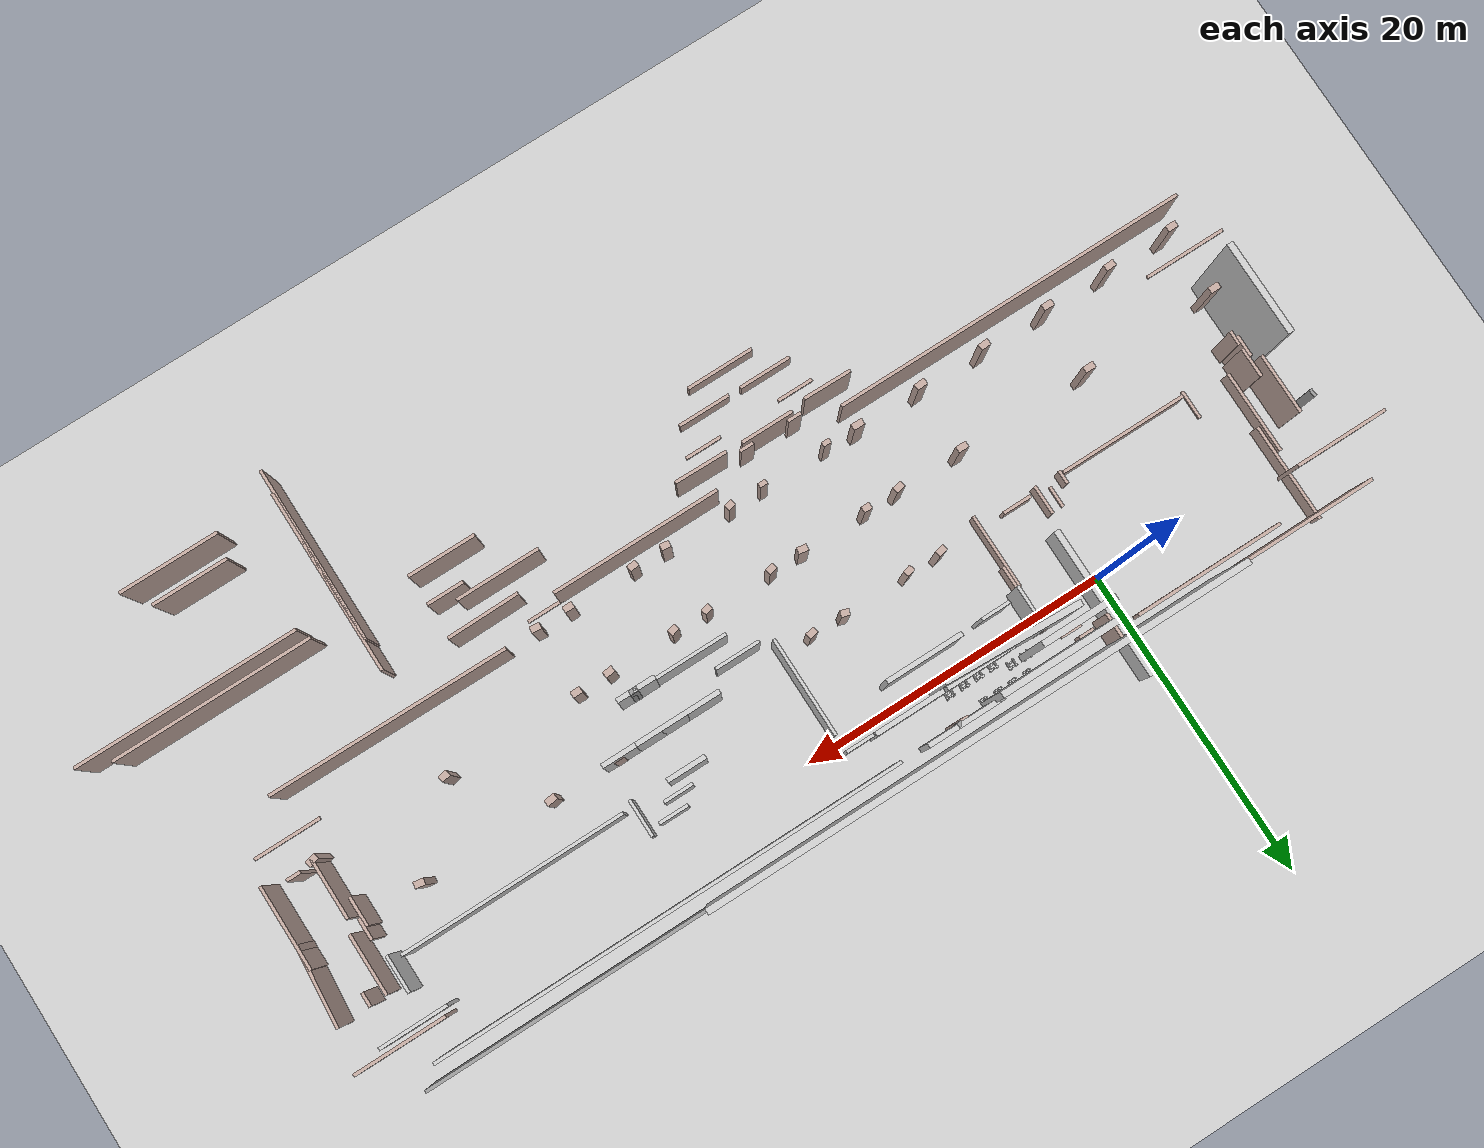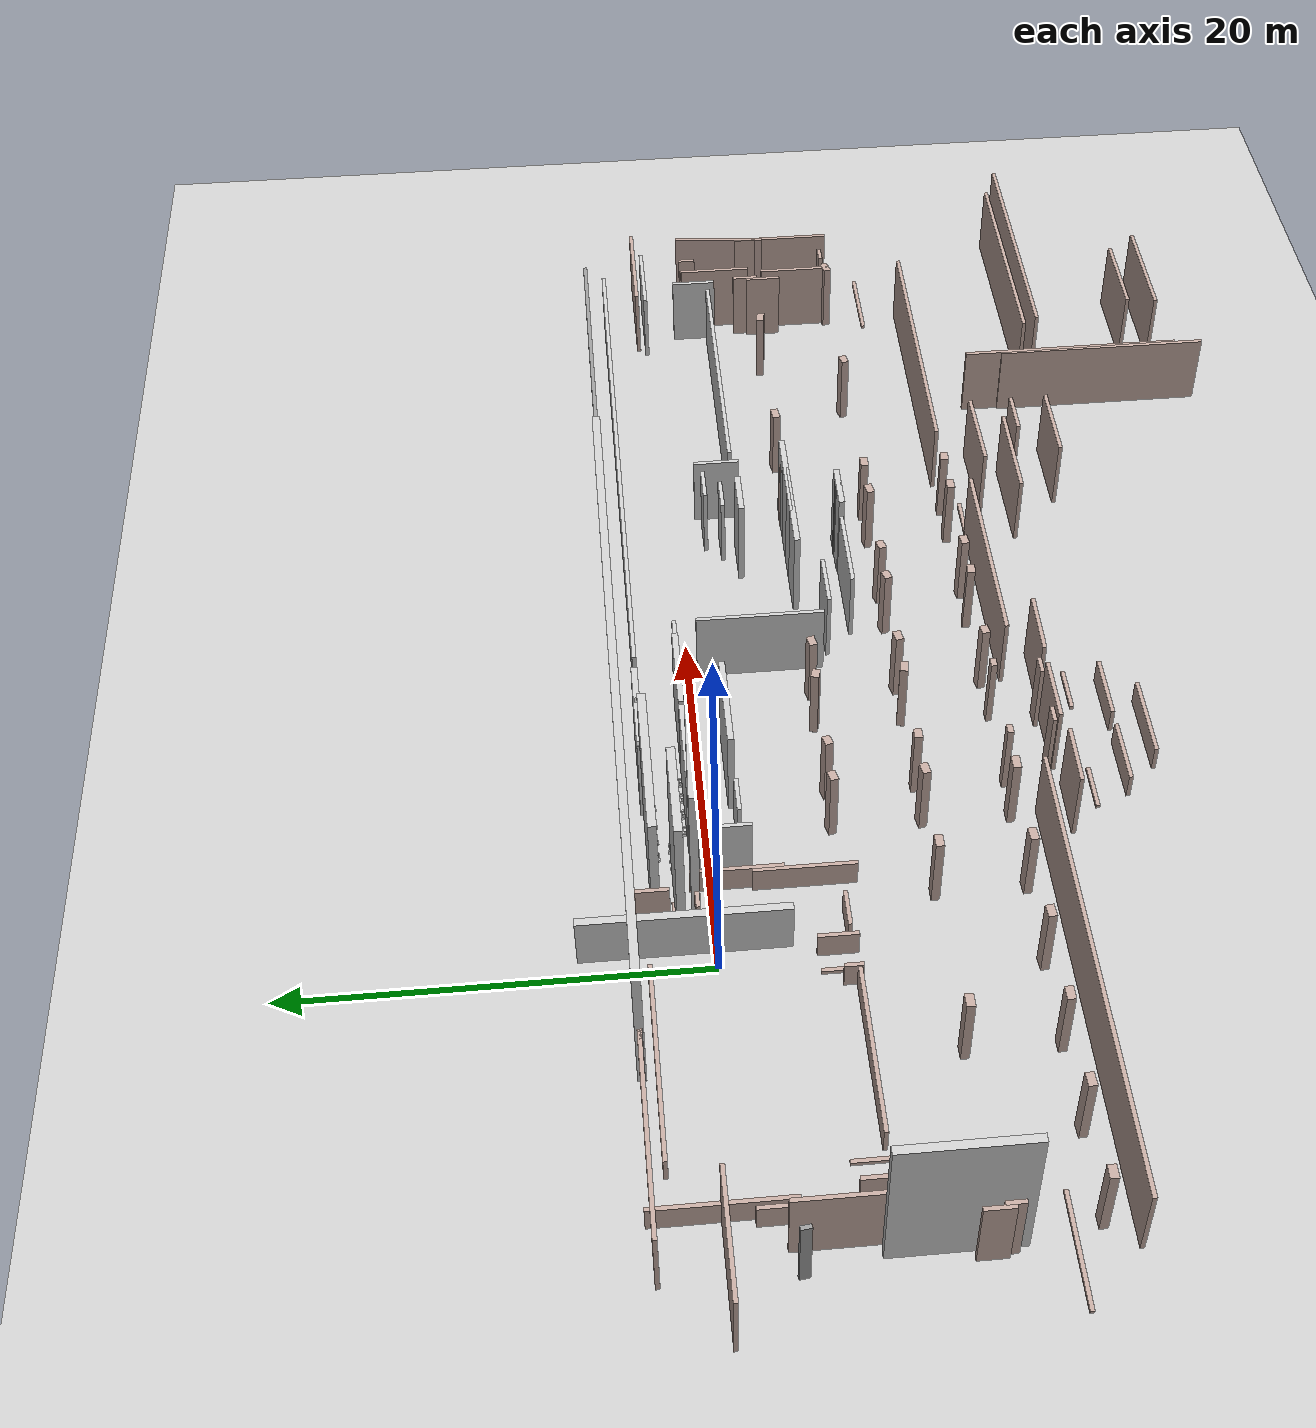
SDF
<?xml version='1.0'?>
<sdf version='1.6'>
  <world name='default'>
    <physics name='1ms' type='ignored'>
      <max_step_size>0.001</max_step_size>
      <real_time_factor>1.0</real_time_factor>
    </physics>
    <plugin filename='gz-sim-physics-system' name='gz::sim::systems::Physics'>
    </plugin>
    <plugin filename='gz-sim-user-commands-system' name='gz::sim::systems::UserCommands'>
    </plugin>
    <plugin filename='gz-sim-scene-broadcaster-system' name='gz::sim::systems::SceneBroadcaster'>
    </plugin>
    <scene>
      <ambient>1.0 1.0 1.0</ambient>
      <background>0.8 0.8 0.8</background>
      <sky></sky>
    </scene>
    <light type='directional' name='sun'>
      <cast_shadows>true</cast_shadows>
      <pose>0 0 10 0 0 0</pose>
      <diffuse>0.5 0.5 0.5 1</diffuse>
      <specular>0.2 0.2 0.2 1</specular>
      <direction>-0.5 0.1 -0.9</direction>
      <attenuation>
        <range>1000</range>
        <constant>0.9</constant>
        <linear>0.01</linear>
        <quadratic>0.001</quadratic>
      </attenuation>
    </light>
    <model name='ground_plane'>
      <static>true</static>
      <link name='link'>
        <collision name='collision'>
          <geometry>
            <plane>
              <normal>0 0 1</normal>
              <size>400 400</size>
            </plane>
          </geometry>
        </collision>
        <visual name='visual'>
          <geometry>
            <plane>
              <normal>0 0 1</normal>
              <size>400 400</size>
            </plane>
          </geometry>
          <material>
            <ambient>0.8 0.8 0.8 1</ambient>
            <diffuse>0.8 0.8 0.8 1</diffuse>
            <specular>0.8 0.8 0.8 1</specular>
          </material>
        </visual>
      </link>
    </model>

    <!-- Include Gedung P building model with corrected offset -->
    <include>
      <uri>file:///home/nuby/bcr_ws/src/bcr_bot/models/gedung_p/model.sdf</uri>
      <pose>17.79816 -12.54414 0 0 0 0</pose>
    </include>

    <!-- Front Side Chairs (kursi_corak) -->
    <!-- Horizontal line of 4 chairs -->
    <include>
      <uri>model://kursi_corak</uri>
      <pose>8.0 1.0 0 0 0 0</pose>
    </include>
    <include>
      <uri>model://kursi_corak</uri>
      <pose>9.0 1.0 0 0 0 0</pose>
    </include>
    <include>
      <uri>model://kursi_corak</uri>
      <pose>10.0 1.0 0 0 0 0</pose>
    </include>
    <include>
      <uri>model://kursi_corak</uri>
      <pose>11.0 1.0 0 0 0 0</pose>
    </include>

    <!-- Additional chairs in front area -->
    <include>
      <uri>model://kursi_corak</uri>
      <pose>6.0 1.5 0 0 0 0</pose>
    </include>
    <include>
      <uri>model://kursi_corak</uri>
      <pose>7.0 1.5 0 0 0 0</pose>
    </include>

    <!-- Rotated chairs at y=2.5 -->
    <include>
      <uri>model://kursi_corak</uri>
      <pose>6.5 2.5 0 0 0 1.57</pose>
    </include>
    <include>
      <uri>model://kursi_corak</uri>
      <pose>7.5 2.5 0 0 0 1.57</pose>
    </include>
    <include>
      <uri>model://kursi_corak</uri>
      <pose>8.5 2.5 0 0 0 1.57</pose>
    </include>
    <include>
      <uri>model://kursi_corak</uri>
      <pose>9.5 2.5 0 0 0 1.57</pose>
    </include>
  </world>
</sdf>

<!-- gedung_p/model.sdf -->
<sdf version='1.6'>
  <model name='gedung_p'>
    <pose frame="">0.101024 2.54038 0.0 0.0 -0.0 0.0</pose>
    <link name='Wall_104'>
      <collision name='Wall_104_Collision'>
        <geometry>
          <box>
            <size>2.89974 0.2 4.0</size>
          </box>
        </geometry>
        <pose frame="">0.0 0.0 2.0 0.0 -0.0 0.0</pose>
      </collision>
      <visual name='Wall_104_Visual'>
        <pose frame="">0.0 0.0 2.0 0.0 -0.0 0.0</pose>
        <geometry>
          <box>
            <size>2.89974 0.2 4.0</size>
          </box>
        </geometry>
        <material>
          <ambient>0.8 0.8 0.8 1</ambient>
          <diffuse>0.8 0.8 0.8 1</diffuse>
        </material>
        <meta>
          <layer>0</layer>
        </meta>
      </visual>
      <pose frame="">-12.83302 12.00262 0.0 0.0 -0.0 -1.571844</pose>
    </link>
    <link name='Wall_105'>
      <collision name='Wall_105_Collision'>
        <geometry>
          <box>
            <size>1.9 0.2 4.0</size>
          </box>
        </geometry>
        <pose frame="">0.0 0.0 2.0 0.0 -0.0 0.0</pose>
      </collision>
      <visual name='Wall_105_Visual'>
        <pose frame="">0.0 0.0 2.0 0.0 -0.0 0.0</pose>
        <geometry>
          <box>
            <size>1.9 0.2 4.0</size>
          </box>
        </geometry>
        <material>
          <ambient>0.8 0.8 0.8 1</ambient>
          <diffuse>0.8 0.8 0.8 1</diffuse>
        </material>
        <meta>
          <layer>0</layer>
        </meta>
      </visual>
      <pose frame="">-11.02902 11.04762 0.0 0.0 -0.0 0.0</pose>
    </link>
    <link name='Wall_108'>
      <collision name='Wall_108_Collision'>
        <geometry>
          <box>
            <size>5.0 0.3 5.0</size>
          </box>
        </geometry>
        <pose frame="">0.0 0.0 2.5 0.0 -0.0 0.0</pose>
      </collision>
      <visual name='Wall_108_Visual'>
        <pose frame="">0.0 0.0 2.5 0.0 -0.0 0.0</pose>
        <geometry>
          <box>
            <size>5.0 0.3 5.0</size>
          </box>
        </geometry>
        <material>
          <ambient>0.8 0.8 0.8 1</ambient>
          <diffuse>0.8 0.8 0.8 1</diffuse>
        </material>
        <meta>
          <layer>0</layer>
        </meta>
      </visual>
      <pose frame="">-6.09502 15.3396 0.0 0.0 -0.0 0.0</pose>
    </link>
    <link name='Wall_11'>
      <collision name='Wall_11_Collision'>
        <geometry>
          <box>
            <size>6.0 0.4 8.0</size>
          </box>
        </geometry>
        <pose frame="">0.0 0.0 4.0 0.0 -0.0 0.0</pose>
      </collision>
      <visual name='Wall_11_Visual'>
        <pose frame="">0.0 0.0 4.0 0.0 -0.0 0.0</pose>
        <geometry>
          <box>
            <size>6.0 0.4 8.0</size>
          </box>
        </geometry>
        <material>
          <ambient>0.8 0.8 0.8 1</ambient>
          <diffuse>0.8 0.8 0.8 1</diffuse>
        </material>
        <meta>
          <layer>0</layer>
        </meta>
      </visual>
      <pose frame="">-32.385 4.11362 0.0 0.0 -0.0 1.570796</pose>
    </link>
    <link name='Wall_116'>
      <collision name='Wall_116_Collision'>
        <geometry>
          <box>
            <size>4.80184 0.4 0.4</size>
          </box>
        </geometry>
        <pose frame="">0.0 0.0 0.2 0.0 -0.0 0.0</pose>
      </collision>
      <visual name='Wall_116_Visual'>
        <pose frame="">0.0 0.0 0.2 0.0 -0.0 0.0</pose>
        <geometry>
          <box>
            <size>4.80184 0.4 0.4</size>
          </box>
        </geometry>
        <material>
          <ambient>1 1 1 1</ambient>
          <diffuse>1 1 1 1</diffuse>
        </material>
        <meta>
          <layer>0</layer>
        </meta>
      </visual>
      <pose frame="">-15.64302 16.3096 0.0 0.0 -0.0 6.28318</pose>
    </link>
    <link name='Wall_119'>
      <collision name='Wall_119_Collision'>
        <geometry>
          <box>
            <size>34.8 0.4 8.0</size>
          </box>
        </geometry>
        <pose frame="">0.0 0.0 4.0 0.0 -0.0 0.0</pose>
      </collision>
      <visual name='Wall_119_Visual'>
        <pose frame="">0.0 0.0 4.0 0.0 -0.0 0.0</pose>
        <geometry>
          <box>
            <size>34.8 0.4 8.0</size>
          </box>
        </geometry>
        <material>
          <ambient>0.8 0.8 0.8 1</ambient>
          <diffuse>0.8 0.8 0.8 1</diffuse>
        </material>
        <meta>
          <layer>0</layer>
        </meta>
      </visual>
      <pose frame="">-5.94302 16.3096 0.0 0.0 -0.0 0.0</pose>
    </link>
    <link name='Wall_122'>
      <collision name='Wall_122_Collision'>
        <geometry>
          <box>
            <size>9.8 0.4 2.8</size>
          </box>
        </geometry>
        <pose frame="">0.0 0.0 1.4 0.0 -0.0 0.0</pose>
      </collision>
      <visual name='Wall_122_Visual'>
        <pose frame="">0.0 0.0 1.4 0.0 -0.0 0.0</pose>
        <geometry>
          <box>
            <size>9.8 0.4 2.8</size>
          </box>
        </geometry>
        <material>
          <ambient>0.8 0.8 0.8 1</ambient>
          <diffuse>0.8 0.8 0.8 1</diffuse>
        </material>
        <meta>
          <layer>0</layer>
        </meta>
      </visual>
      <pose frame="">-16.69702 13.9496 0.0 0.0 -0.0 -1.570796</pose>
    </link>
    <link name='Wall_124'>
      <collision name='Wall_124_Collision'>
        <geometry>
          <box>
            <size>4.8 0.4 8.0</size>
          </box>
        </geometry>
        <pose frame="">0.0 0.0 4.0 0.0 -0.0 0.0</pose>
      </collision>
      <visual name='Wall_124_Visual'>
        <pose frame="">0.0 0.0 4.0 0.0 -0.0 0.0</pose>
        <geometry>
          <box>
            <size>4.8 0.4 8.0</size>
          </box>
        </geometry>
        <material>
          <ambient>0.8 0.8 0.8 1</ambient>
          <diffuse>0.8 0.8 0.8 1</diffuse>
        </material>
        <meta>
          <layer>0</layer>
        </meta>
      </visual>
      <pose frame="">-13.78702 14.05762 0.0 0.0 -0.0 3.1416</pose>
    </link>
    <link name='Wall_125'>
      <collision name='Wall_125_Collision'>
        <geometry>
          <box>
            <size>7.8 0.4 8.0</size>
          </box>
        </geometry>
        <pose frame="">0.0 0.0 4.0 0.0 -0.0 0.0</pose>
      </collision>
      <visual name='Wall_125_Visual'>
        <pose frame="">0.0 0.0 4.0 0.0 -0.0 0.0</pose>
        <geometry>
          <box>
            <size>7.8 0.4 8.0</size>
          </box>
        </geometry>
        <material>
          <ambient>0.8 0.8 0.8 1</ambient>
          <diffuse>0.8 0.8 0.8 1</diffuse>
        </material>
        <meta>
          <layer>0</layer>
        </meta>
      </visual>
      <pose frame="">-11.93702 15.15762 0.0 0.0 -0.0 0.0</pose>
    </link>
    <link name='Wall_126'>
      <collision name='Wall_126_Collision'>
        <geometry>
          <box>
            <size>8.62204 0.4 8.0</size>
          </box>
        </geometry>
        <pose frame="">0.0 0.0 4.0 0.0 -0.0 0.0</pose>
      </collision>
      <visual name='Wall_126_Visual'>
        <pose frame="">0.0 0.0 4.0 0.0 -0.0 0.0</pose>
        <geometry>
          <box>
            <size>8.62204 0.4 8.0</size>
          </box>
        </geometry>
        <material>
          <ambient>0.8 0.8 0.8 1</ambient>
          <diffuse>0.8 0.8 0.8 1</diffuse>
        </material>
        <meta>
          <layer>0</layer>
        </meta>
      </visual>
      <pose frame="">-10.13302 13.10262 0.0 0.0 -0.0 -3.18636</pose>
    </link>
    <link name='Wall_128'>
      <collision name='Wall_128_Collision'>
        <geometry>
          <box>
            <size>4.5 0.3 5.0</size>
          </box>
        </geometry>
        <pose frame="">0.0 0.0 2.5 0.0 -0.0 0.0</pose>
      </collision>
      <visual name='Wall_128_Visual'>
        <pose frame="">0.0 0.0 2.5 0.0 -0.0 0.0</pose>
        <geometry>
          <box>
            <size>4.5 0.3 5.0</size>
          </box>
        </geometry>
        <material>
          <ambient>0.8 0.8 0.8 1</ambient>
          <diffuse>0.8 0.8 0.8 1</diffuse>
        </material>
        <meta>
          <layer>0</layer>
        </meta>
      </visual>
      <pose frame="">-8.44502 13.23962 0.0 0.0 -0.0 -3.1416</pose>
    </link>
    <link name='Wall_129'>
      <collision name='Wall_129_Collision'>
        <geometry>
          <box>
            <size>5.0 0.3 5.0</size>
          </box>
        </geometry>
        <pose frame="">0.0 0.0 2.5 0.0 -0.0 0.0</pose>
      </collision>
      <visual name='Wall_129_Visual'>
        <pose frame="">0.0 0.0 2.5 0.0 -0.0 0.0</pose>
        <geometry>
          <box>
            <size>5.0 0.3 5.0</size>
          </box>
        </geometry>
        <material>
          <ambient>0.8 0.8 0.8 1</ambient>
          <diffuse>0.8 0.8 0.8 1</diffuse>
        </material>
        <meta>
          <layer>0</layer>
        </meta>
      </visual>
      <pose frame="">-6.09502 11.1396 0.0 0.0 -0.0 0.0</pose>
    </link>
    <link name='Wall_130'>
      <collision name='Wall_130_Collision'>
        <geometry>
          <box>
            <size>4.5 0.3 5.0</size>
          </box>
        </geometry>
        <pose frame="">0.0 0.0 2.5 0.0 -0.0 0.0</pose>
      </collision>
      <visual name='Wall_130_Visual'>
        <pose frame="">0.0 0.0 2.5 0.0 -0.0 0.0</pose>
        <geometry>
          <box>
            <size>4.5 0.3 5.0</size>
          </box>
        </geometry>
        <material>
          <ambient>0.8 0.8 0.8 1</ambient>
          <diffuse>0.8 0.8 0.8 1</diffuse>
        </material>
        <meta>
          <layer>0</layer>
        </meta>
      </visual>
      <pose frame="">-3.74502 13.23962 0.0 0.0 -0.0 3.1416</pose>
    </link>
    <link name='Wall_132'>
      <collision name='Wall_132_Collision'>
        <geometry>
          <box>
            <size>4.40008 0.2 4.0</size>
          </box>
        </geometry>
        <pose frame="">0.0 0.0 2.0 0.0 -0.0 0.0</pose>
      </collision>
      <visual name='Wall_132_Visual'>
        <pose frame="">0.0 0.0 2.0 0.0 -0.0 0.0</pose>
        <geometry>
          <box>
            <size>4.40008 0.2 4.0</size>
          </box>
        </geometry>
        <material>
          <ambient>0.8 0.8 0.8 1</ambient>
          <diffuse>0.8 0.8 0.8 1</diffuse>
        </material>
        <meta>
          <layer>0</layer>
        </meta>
      </visual>
      <pose frame="">-1.887024 13.1816 0.0 0.0 -0.0 -3.1416</pose>
    </link>
    <link name='Wall_137'>
      <collision name='Wall_137_Collision'>
        <geometry>
          <box>
            <size>6.40062 0.2 4.0</size>
          </box>
        </geometry>
        <pose frame="">0.0 0.0 2.0 0.0 -0.0 0.0</pose>
      </collision>
      <visual name='Wall_137_Visual'>
        <pose frame="">0.0 0.0 2.0 0.0 -0.0 0.0</pose>
        <geometry>
          <box>
            <size>6.40062 0.2 4.0</size>
          </box>
        </geometry>
        <material>
          <ambient>0.8 0.8 0.8 1</ambient>
          <diffuse>0.8 0.8 0.8 1</diffuse>
        </material>
        <meta>
          <layer>0</layer>
        </meta>
      </visual>
      <pose frame="">0.304976 8.8896 0.0 0.0 -0.0 -1.570796</pose>
    </link>
    <link name='Wall_138'>
      <collision name='Wall_138_Collision'>
        <geometry>
          <box>
            <size>2.90014 0.2 4.0</size>
          </box>
        </geometry>
        <pose frame="">0.0 0.0 2.0 0.0 -0.0 0.0</pose>
      </collision>
      <visual name='Wall_138_Visual'>
        <pose frame="">0.0 0.0 2.0 0.0 -0.0 0.0</pose>
        <geometry>
          <box>
            <size>2.90014 0.2 4.0</size>
          </box>
        </geometry>
        <material>
          <ambient>0.8 0.8 0.8 1</ambient>
          <diffuse>0.8 0.8 0.8 1</diffuse>
        </material>
        <meta>
          <layer>0</layer>
        </meta>
      </visual>
      <pose frame="">2.49698 5.34762 0.0 0.0 -0.0 -3.1416</pose>
    </link>
    <link name='Wall_139'>
      <collision name='Wall_139_Collision'>
        <geometry>
          <box>
            <size>4.90086 0.2 4.0</size>
          </box>
        </geometry>
        <pose frame="">0.0 0.0 2.0 0.0 -0.0 0.0</pose>
      </collision>
      <visual name='Wall_139_Visual'>
        <pose frame="">0.0 0.0 2.0 0.0 -0.0 0.0</pose>
        <geometry>
          <box>
            <size>4.90086 0.2 4.0</size>
          </box>
        </geometry>
        <material>
          <ambient>0.8 0.8 0.8 1</ambient>
          <diffuse>0.8 0.8 0.8 1</diffuse>
        </material>
        <meta>
          <layer>0</layer>
        </meta>
      </visual>
      <pose frame="">4.84698 3.9976 0.0 0.0 -0.0 0.0</pose>
    </link>
    <link name='Wall_140'>
      <collision name='Wall_140_Collision'>
        <geometry>
          <box>
            <size>5.5 0.3 5.0</size>
          </box>
        </geometry>
        <pose frame="">0.0 0.0 2.5 0.0 -0.0 0.0</pose>
      </collision>
      <visual name='Wall_140_Visual'>
        <pose frame="">0.0 0.0 2.5 0.0 -0.0 0.0</pose>
        <geometry>
          <box>
            <size>5.5 0.3 5.0</size>
          </box>
        </geometry>
        <material>
          <ambient>0.8 0.8 0.8 1</ambient>
          <diffuse>0.8 0.8 0.8 1</diffuse>
        </material>
        <meta>
          <layer>0</layer>
        </meta>
      </visual>
      <pose frame="">7.19698 6.59762 0.0 0.0 -0.0 3.1416</pose>
    </link>
    <link name='Wall_141'>
      <collision name='Wall_141_Collision'>
        <geometry>
          <box>
            <size>2.5 0.3 5.0</size>
          </box>
        </geometry>
        <pose frame="">0.0 0.0 2.5 0.0 -0.0 0.0</pose>
      </collision>
      <visual name='Wall_141_Visual'>
        <pose frame="">0.0 0.0 2.5 0.0 -0.0 0.0</pose>
        <geometry>
          <box>
            <size>2.5 0.3 5.0</size>
          </box>
        </geometry>
        <material>
          <ambient>0.8 0.8 0.8 1</ambient>
          <diffuse>0.8 0.8 0.8 1</diffuse>
        </material>
        <meta>
          <layer>0</layer>
        </meta>
      </visual>
      <pose frame="">8.29698 9.1976 0.0 0.0 -0.0 0.0</pose>
    </link>
    <link name='Wall_142'>
      <collision name='Wall_142_Collision'>
        <geometry>
          <box>
            <size>5.5 0.3 5.0</size>
          </box>
        </geometry>
        <pose frame="">0.0 0.0 2.5 0.0 -0.0 0.0</pose>
      </collision>
      <visual name='Wall_142_Visual'>
        <pose frame="">0.0 0.0 2.5 0.0 -0.0 0.0</pose>
        <geometry>
          <box>
            <size>5.5 0.3 5.0</size>
          </box>
        </geometry>
        <material>
          <ambient>0.8 0.8 0.8 1</ambient>
          <diffuse>0.8 0.8 0.8 1</diffuse>
        </material>
        <meta>
          <layer>0</layer>
        </meta>
      </visual>
      <pose frame="">9.39698 6.59762 0.0 0.0 -0.0 -3.1416</pose>
    </link>
    <link name='Wall_143'>
      <collision name='Wall_143_Collision'>
        <geometry>
          <box>
            <size>2.5 0.3 5.0</size>
          </box>
        </geometry>
        <pose frame="">0.0 0.0 2.5 0.0 -0.0 0.0</pose>
      </collision>
      <visual name='Wall_143_Visual'>
        <pose frame="">0.0 0.0 2.5 0.0 -0.0 0.0</pose>
        <geometry>
          <box>
            <size>2.5 0.3 5.0</size>
          </box>
        </geometry>
        <material>
          <ambient>0.8 0.8 0.8 1</ambient>
          <diffuse>0.8 0.8 0.8 1</diffuse>
        </material>
        <meta>
          <layer>0</layer>
        </meta>
      </visual>
      <pose frame="">8.29698 3.9976 0.0 0.0 -0.0 6.28318</pose>
    </link>
    <link name='Wall_145'>
      <collision name='Wall_145_Collision'>
        <geometry>
          <box>
            <size>30.5 0.2 4.0</size>
          </box>
        </geometry>
        <pose frame="">0.0 0.0 2.0 0.0 -0.0 0.0</pose>
      </collision>
      <visual name='Wall_145_Visual'>
        <pose frame="">0.0 0.0 2.0 0.0 -0.0 0.0</pose>
        <geometry>
          <box>
            <size>30.5 0.2 4.0</size>
          </box>
        </geometry>
        <material>
          <ambient>0.8 0.8 0.8 1</ambient>
          <diffuse>0.8 0.8 0.8 1</diffuse>
        </material>
        <meta>
          <layer>0</layer>
        </meta>
      </visual>
      <pose frame="">13.26298 15.28162 0.0 0.0 -0.0 0.0</pose>
    </link>
    <link name='Wall_147'>
      <collision name='Wall_147_Collision'>
        <geometry>
          <box>
            <size>2.4 0.2 0.2</size>
          </box>
        </geometry>
        <pose frame="">0.0 0.0 0.1 0.0 -0.0 0.0</pose>
      </collision>
      <visual name='Wall_147_Visual'>
        <pose frame="">0.0 0.0 0.1 0.0 -0.0 0.0</pose>
        <geometry>
          <box>
            <size>2.4 0.2 0.2</size>
          </box>
        </geometry>
        <material>
          <ambient>0.8 0.8 0.8 1</ambient>
          <diffuse>0.8 0.8 0.8 1</diffuse>
        </material>
        <meta>
          <layer>0</layer>
        </meta>
      </visual>
      <pose frame="">3.75698 16.3096 0.0 0.0 -0.0 0.0</pose>
    </link>
    <link name='Wall_149'>
      <collision name='Wall_149_Collision'>
        <geometry>
          <box>
            <size>1.9 0.2 4.0</size>
          </box>
        </geometry>
        <pose frame="">0.0 0.0 2.0 0.0 -0.0 0.0</pose>
      </collision>
      <visual name='Wall_149_Visual'>
        <pose frame="">0.0 0.0 2.0 0.0 -0.0 0.0</pose>
        <geometry>
          <box>
            <size>1.9 0.2 4.0</size>
          </box>
        </geometry>
        <material>
          <ambient>0.8 0.8 0.8 1</ambient>
          <diffuse>0.8 0.8 0.8 1</diffuse>
        </material>
        <meta>
          <layer>0</layer>
        </meta>
      </visual>
      <pose frame="">9.39698 10.04762 0.0 0.0 -0.0 3.1416</pose>
    </link>
    <link name='Wall_150'>
      <collision name='Wall_150_Collision'>
        <geometry>
          <box>
            <size>1.9 0.2 4.0</size>
          </box>
        </geometry>
        <pose frame="">0.0 0.0 2.0 0.0 -0.0 0.0</pose>
      </collision>
      <visual name='Wall_150_Visual'>
        <pose frame="">0.0 0.0 2.0 0.0 -0.0 0.0</pose>
        <geometry>
          <box>
            <size>1.9 0.2 4.0</size>
          </box>
        </geometry>
        <material>
          <ambient>0.8 0.8 0.8 1</ambient>
          <diffuse>0.8 0.8 0.8 1</diffuse>
        </material>
        <meta>
          <layer>0</layer>
        </meta>
      </visual>
      <pose frame="">10.24698 10.89762 0.0 0.0 -0.0 0.0</pose>
    </link>
    <link name='Wall_151'>
      <collision name='Wall_151_Collision'>
        <geometry>
          <box>
            <size>2.4 0.2 4.0</size>
          </box>
        </geometry>
        <pose frame="">0.0 0.0 2.0 0.0 -0.0 0.0</pose>
      </collision>
      <visual name='Wall_151_Visual'>
        <pose frame="">0.0 0.0 2.0 0.0 -0.0 0.0</pose>
        <geometry>
          <box>
            <size>2.4 0.2 4.0</size>
          </box>
        </geometry>
        <material>
          <ambient>0.8 0.8 0.8 1</ambient>
          <diffuse>0.8 0.8 0.8 1</diffuse>
        </material>
        <meta>
          <layer>0</layer>
        </meta>
      </visual>
      <pose frame="">11.87498 10.1196 0.0 0.0 -0.0 -1.570796</pose>
    </link>
    <link name='Wall_152'>
      <collision name='Wall_152_Collision'>
        <geometry>
          <box>
            <size>14.4 0.2 4.0</size>
          </box>
        </geometry>
        <pose frame="">0.0 0.0 2.0 0.0 -0.0 0.0</pose>
      </collision>
      <visual name='Wall_152_Visual'>
        <pose frame="">0.0 0.0 2.0 0.0 -0.0 0.0</pose>
        <geometry>
          <box>
            <size>14.4 0.2 4.0</size>
          </box>
        </geometry>
        <material>
          <ambient>0.8 0.8 0.8 1</ambient>
          <diffuse>0.8 0.8 0.8 1</diffuse>
        </material>
        <meta>
          <layer>0</layer>
        </meta>
      </visual>
      <pose frame="">19.75298 9.3416 0.0 0.0 -0.0 0.0</pose>
    </link>
    <link name='Wall_154'>
      <collision name='Wall_154_Collision'>
        <geometry>
          <box>
            <size>2.40052 0.2 4.0</size>
          </box>
        </geometry>
        <pose frame="">0.0 0.0 2.0 0.0 -0.0 0.0</pose>
      </collision>
      <visual name='Wall_154_Visual'>
        <pose frame="">0.0 0.0 2.0 0.0 -0.0 0.0</pose>
        <geometry>
          <box>
            <size>2.40052 0.2 4.0</size>
          </box>
        </geometry>
        <material>
          <ambient>0.8 0.8 0.8 1</ambient>
          <diffuse>0.8 0.8 0.8 1</diffuse>
        </material>
        <meta>
          <layer>0</layer>
        </meta>
      </visual>
      <pose frame="">27.631 10.1196 0.0 0.0 -0.0 1.570796</pose>
    </link>
    <link name='Wall_155'>
      <collision name='Wall_155_Collision'>
        <geometry>
          <box>
            <size>4.39964 0.2 4.0</size>
          </box>
        </geometry>
        <pose frame="">0.0 0.0 2.0 0.0 -0.0 0.0</pose>
      </collision>
      <visual name='Wall_155_Visual'>
        <pose frame="">0.0 0.0 2.0 0.0 -0.0 0.0</pose>
        <geometry>
          <box>
            <size>4.39964 0.2 4.0</size>
          </box>
        </geometry>
        <material>
          <ambient>0.8 0.8 0.8 1</ambient>
          <diffuse>0.8 0.8 0.8 1</diffuse>
        </material>
        <meta>
          <layer>0</layer>
        </meta>
      </visual>
      <pose frame="">28.409 12.9976 0.0 0.0 -0.0 3.1416</pose>
    </link>
    <link name='Wall_157'>
      <collision name='Wall_157_Collision'>
        <geometry>
          <box>
            <size>24.9 0.2 4.0</size>
          </box>
        </geometry>
        <pose frame="">0.0 0.0 2.0 0.0 -0.0 0.0</pose>
      </collision>
      <visual name='Wall_157_Visual'>
        <pose frame="">0.0 0.0 2.0 0.0 -0.0 0.0</pose>
        <geometry>
          <box>
            <size>24.9 0.2 4.0</size>
          </box>
        </geometry>
        <material>
          <ambient>0.8 0.8 0.8 1</ambient>
          <script>
            <uri>file://media/materials/scripts/gazebo.material</uri>
            <name>Gazebo/Grey</name>
          </script>
          <ambient>0.760784 0.662745 0.627451 1</ambient>
        </material>
        <meta>
          <layer>0</layer>
        </meta>
      </visual>
      <pose frame="">17.20698 16.3096 0.0 0.0 -0.0 0.0</pose>
    </link>
    <link name='Wall_159'>
      <collision name='Wall_159_Collision'>
        <geometry>
          <box>
            <size>5.9 0.2 4.0</size>
          </box>
        </geometry>
        <pose frame="">0.0 0.0 2.0 0.0 -0.0 0.0</pose>
      </collision>
      <visual name='Wall_159_Visual'>
        <pose frame="">0.0 0.0 2.0 0.0 -0.0 0.0</pose>
        <geometry>
          <box>
            <size>5.9 0.2 4.0</size>
          </box>
        </geometry>
        <material>
          <script>
            <uri>file://media/materials/scripts/gazebo.material</uri>
            <name>Gazebo/Grey</name>
          </script>
          <ambient>0.760784 0.662745 0.627451 1</ambient>
        </material>
        <meta>
          <layer>0</layer>
        </meta>
      </visual>
      <pose frame="">29.557 13.4596 0.0 0.0 -0.0 -3.1416</pose>
    </link>
    <link name='Wall_161'>
      <collision name='Wall_161_Collision'>
        <geometry>
          <box>
            <size>0.898622 0.2 4.0</size>
          </box>
        </geometry>
        <pose frame="">0.0 0.0 2.0 0.0 -0.0 0.0</pose>
      </collision>
      <visual name='Wall_161_Visual'>
        <pose frame="">0.0 0.0 2.0 0.0 -0.0 0.0</pose>
        <geometry>
          <box>
            <size>0.898622 0.2 4.0</size>
          </box>
        </geometry>
        <material>
          <script>
            <uri>file://media/materials/scripts/gazebo.material</uri>
            <name>Gazebo/Grey</name>
          </script>
          <ambient>0.760784 0.662745 0.627451 1</ambient>
        </material>
        <meta>
          <layer>0</layer>
        </meta>
      </visual>
      <pose frame="">29.804 10.36262 0.0 0.0 -0.0 -1.570796</pose>
    </link>
    <link name='Wall_162'>
      <collision name='Wall_162_Collision'>
        <geometry>
          <box>
            <size>3.9 0.2 4.0</size>
          </box>
        </geometry>
        <pose frame="">0.0 0.0 2.0 0.0 -0.0 0.0</pose>
      </collision>
      <visual name='Wall_162_Visual'>
        <pose frame="">0.0 0.0 2.0 0.0 -0.0 0.0</pose>
        <geometry>
          <box>
            <size>3.9 0.2 4.0</size>
          </box>
        </geometry>
        <material>
          <script>
            <uri>file://media/materials/scripts/gazebo.material</uri>
            <name>Gazebo/Grey</name>
          </script>
          <ambient>0.760784 0.662745 0.627451 1</ambient>
        </material>
        <meta>
          <layer>0</layer>
        </meta>
      </visual>
      <pose frame="">28.743 8.8066 0.0 0.0 -0.0 -4.71162</pose>
    </link>
    <link name='Wall_164'>
      <collision name='Wall_164_Collision'>
        <geometry>
          <box>
            <size>1.399964 0.2 4.0</size>
          </box>
        </geometry>
        <pose frame="">0.0 0.0 2.0 0.0 -0.0 0.0</pose>
      </collision>
      <visual name='Wall_164_Visual'>
        <pose frame="">0.0 0.0 2.0 0.0 -0.0 0.0</pose>
        <geometry>
          <box>
            <size>1.399964 0.2 4.0</size>
          </box>
        </geometry>
        <material>
          <script>
            <uri>file://media/materials/scripts/gazebo.material</uri>
            <name>Gazebo/Grey</name>
          </script>
          <ambient>0.760784 0.662745 0.627451 1</ambient>
        </material>
        <meta>
          <layer>0</layer>
        </meta>
      </visual>
      <pose frame="">27.86 7.07362 0.0 0.0 -0.0 -1.56844</pose>
    </link>
    <link name='Wall_165'>
      <collision name='Wall_165_Collision'>
        <geometry>
          <box>
            <size>1.900418 0.2 4.0</size>
          </box>
        </geometry>
        <pose frame="">0.0 0.0 2.0 0.0 -0.0 0.0</pose>
      </collision>
      <visual name='Wall_165_Visual'>
        <pose frame="">0.0 0.0 2.0 0.0 -0.0 0.0</pose>
        <geometry>
          <box>
            <size>1.900418 0.2 4.0</size>
          </box>
        </geometry>
        <material>
          <script>
            <uri>file://media/materials/scripts/gazebo.material</uri>
            <name>Gazebo/Grey</name>
          </script>
          <ambient>0.760784 0.662745 0.627451 1</ambient>
        </material>
        <meta>
          <layer>0</layer>
        </meta>
      </visual>
      <pose frame="">27.684 6.04862 0.0 0.0 -0.0 -4.71238</pose>
    </link>
    <link name='Wall_166'>
      <collision name='Wall_166_Collision'>
        <geometry>
          <box>
            <size>3.8993 0.2 4.0</size>
          </box>
        </geometry>
        <pose frame="">0.0 0.0 2.0 0.0 -0.0 0.0</pose>
      </collision>
      <visual name='Wall_166_Visual'>
        <pose frame="">0.0 0.0 2.0 0.0 -0.0 0.0</pose>
        <geometry>
          <box>
            <size>3.8993 0.2 4.0</size>
          </box>
        </geometry>
        <material>
          <script>
            <uri>file://media/materials/scripts/gazebo.material</uri>
            <name>Gazebo/Grey</name>
          </script>
          <ambient>0.760784 0.662745 0.627451 1</ambient>
        </material>
        <meta>
          <layer>0</layer>
        </meta>
      </visual>
      <pose frame="">28.391 4.13962 0.0 0.0 -0.0 -1.570796</pose>
    </link>
    <link name='Wall_169'>
      <collision name='Wall_169_Collision'>
        <geometry>
          <box>
            <size>5.39864 0.2 4.0</size>
          </box>
        </geometry>
        <pose frame="">0.0 0.0 2.0 0.0 -0.0 0.0</pose>
      </collision>
      <visual name='Wall_169_Visual'>
        <pose frame="">0.0 0.0 2.0 0.0 -0.0 0.0</pose>
        <geometry>
          <box>
            <size>5.39864 0.2 4.0</size>
          </box>
        </geometry>
        <material>
          <script>
            <uri>file://media/materials/scripts/gazebo.material</uri>
            <name>Gazebo/Grey</name>
          </script>
          <ambient>0.760784 0.662745 0.627451 1</ambient>
        </material>
        <meta>
          <layer>0</layer>
        </meta>
      </visual>
      <pose frame="">31.537 4.6696 0.0 0.0 -0.0 1.570796</pose>
    </link>
    <link name='Wall_17'>
      <collision name='Wall_17_Collision'>
        <geometry>
          <box>
            <size>0.899858 0.2 4.0</size>
          </box>
        </geometry>
        <pose frame="">0.0 0.0 2.0 0.0 -0.0 0.0</pose>
      </collision>
      <visual name='Wall_17_Visual'>
        <pose frame="">0.0 0.0 2.0 0.0 -0.0 0.0</pose>
        <geometry>
          <box>
            <size>0.899858 0.2 4.0</size>
          </box>
        </geometry>
        <material>
          <script>
            <uri>file://media/materials/scripts/gazebo.material</uri>
            <name>Gazebo/Grey</name>
          </script>
          <ambient>0.760784 0.662745 0.627451 1</ambient>
        </material>
        <meta>
          <layer>0</layer>
        </meta>
      </visual>
      <pose frame="">-31.148 5.3506 0.0 0.0 -0.0 1.570796</pose>
    </link>
    <link name='Wall_173'>
      <collision name='Wall_173_Collision'>
        <geometry>
          <box>
            <size>5.10546 0.2 4.0</size>
          </box>
        </geometry>
        <pose frame="">0.0 0.0 2.0 0.0 -0.0 0.0</pose>
      </collision>
      <visual name='Wall_173_Visual'>
        <pose frame="">0.0 0.0 2.0 0.0 -0.0 0.0</pose>
        <geometry>
          <box>
            <size>5.10546 0.2 4.0</size>
          </box>
        </geometry>
        <material>
          <script>
            <uri>file://media/materials/scripts/gazebo.material</uri>
            <name>Gazebo/Grey</name>
          </script>
          <ambient>0.760784 0.662745 0.627451 1</ambient>
        </material>
        <meta>
          <layer>0</layer>
        </meta>
      </visual>
      <pose frame="">31.713 8.3116 0.0 0.0 -0.0 -1.65269</pose>
    </link>
    <link name='Wall_175'>
      <collision name='Wall_175_Collision'>
        <geometry>
          <box>
            <size>0.9 0.2 4.0</size>
          </box>
        </geometry>
        <pose frame="">0.0 0.0 2.0 0.0 -0.0 0.0</pose>
      </collision>
      <visual name='Wall_175_Visual'>
        <pose frame="">0.0 0.0 2.0 0.0 -0.0 0.0</pose>
        <geometry>
          <box>
            <size>0.9 0.2 4.0</size>
          </box>
        </geometry>
        <material>
          <script>
            <uri>file://media/materials/scripts/gazebo.material</uri>
            <name>Gazebo/Grey</name>
          </script>
          <ambient>0.760784 0.662745 0.627451 1</ambient>
        </material>
        <meta>
          <layer>0</layer>
        </meta>
      </visual>
      <pose frame="">29.699 2.4816 0.0 0.0 -0.0 -3.1416</pose>
    </link>
    <link name='Wall_176'>
      <collision name='Wall_176_Collision'>
        <geometry>
          <box>
            <size>4.4 0.2 0.2</size>
          </box>
        </geometry>
        <pose frame="">0.0 0.0 0.1 0.0 -0.0 0.0</pose>
      </collision>
      <visual name='Wall_176_Visual'>
        <pose frame="">0.0 0.0 0.1 0.0 -0.0 0.0</pose>
        <geometry>
          <box>
            <size>4.4 0.2 0.2</size>
          </box>
        </geometry>
        <material>
          <script>
            <uri>file://media/materials/scripts/gazebo.material</uri>
            <name>Gazebo/Grey</name>
          </script>
          <ambient>0.760784 0.662745 0.627451 1</ambient>
        </material>
        <meta>
          <layer>0</layer>
        </meta>
      </visual>
      <pose frame="">29.699 0.03161 0.0 0.0 -0.0 -3.1416</pose>
    </link>
    <link name='Wall_178'>
      <collision name='Wall_178_Collision'>
        <geometry>
          <box>
            <size>14.4 0.2 4.0</size>
          </box>
        </geometry>
        <pose frame="">0.0 0.0 2.0 0.0 -0.0 0.0</pose>
      </collision>
      <visual name='Wall_178_Visual'>
        <pose frame="">0.0 0.0 2.0 0.0 -0.0 0.0</pose>
        <geometry>
          <box>
            <size>14.4 0.2 4.0</size>
          </box>
        </geometry>
        <material>
          <script>
            <uri>file://media/materials/scripts/gazebo.material</uri>
            <name>Gazebo/Grey</name>
          </script>
          <ambient>0.760784 0.662745 0.627451 1</ambient>
        </material>
        <meta>
          <layer>0</layer>
        </meta>
      </visual>
      <pose frame="">29.699 -9.1684 0.0 0.0 -0.0 -3.1416</pose>
    </link>
    <link name='Wall_18'>
      <collision name='Wall_18_Collision'>
        <geometry>
          <box>
            <size>1.4 0.2 4.0</size>
          </box>
        </geometry>
        <pose frame="">0.0 0.0 2.0 0.0 -0.0 0.0</pose>
      </collision>
      <visual name='Wall_18_Visual'>
        <pose frame="">0.0 0.0 2.0 0.0 -0.0 0.0</pose>
        <geometry>
          <box>
            <size>1.4 0.2 4.0</size>
          </box>
        </geometry>
        <material>
          <script>
            <uri>file://media/materials/scripts/gazebo.material</uri>
            <name>Gazebo/Grey</name>
          </script>
          <ambient>0.760784 0.662745 0.627451 1</ambient>
        </material>
        <meta>
          <layer>0</layer>
        </meta>
      </visual>
      <pose frame="">-31.325 6.02262 0.0 0.0 -0.0 4.71004</pose>
    </link>
    <link name='Wall_180'>
      <collision name='Wall_180_Collision'>
        <geometry>
          <box>
            <size>6.4 0.2 4.0</size>
          </box>
        </geometry>
        <pose frame="">0.0 0.0 2.0 0.0 -0.0 0.0</pose>
      </collision>
      <visual name='Wall_180_Visual'>
        <pose frame="">0.0 0.0 2.0 0.0 -0.0 0.0</pose>
        <geometry>
          <box>
            <size>6.4 0.2 4.0</size>
          </box>
        </geometry>
        <material>
          <script>
            <uri>file://media/materials/scripts/gazebo.material</uri>
            <name>Gazebo/Grey</name>
          </script>
          <ambient>0.760784 0.662745 0.627451 1</ambient>
        </material>
        <meta>
          <layer>0</layer>
        </meta>
      </visual>
      <pose frame="">26.599 -16.2684 0.0 0.0 -0.0 6.28318</pose>
    </link>
    <link name='Wall_181'>
      <collision name='Wall_181_Collision'>
        <geometry>
          <box>
            <size>11.4 0.2 4.0</size>
          </box>
        </geometry>
        <pose frame="">0.0 0.0 2.0 0.0 -0.0 0.0</pose>
      </collision>
      <visual name='Wall_181_Visual'>
        <pose frame="">0.0 0.0 2.0 0.0 -0.0 0.0</pose>
        <geometry>
          <box>
            <size>11.4 0.2 4.0</size>
          </box>
        </geometry>
        <material>
          <script>
            <uri>file://media/materials/scripts/gazebo.material</uri>
            <name>Gazebo/Grey</name>
          </script>
          <ambient>0.760784 0.662745 0.627451 1</ambient>
        </material>
        <meta>
          <layer>0</layer>
        </meta>
      </visual>
      <pose frame="">19.53898 -12.30838 0.0 0.0 -0.0 4.71238</pose>
    </link>
    <link name='Wall_182'>
      <collision name='Wall_182_Collision'>
        <geometry>
          <box>
            <size>4.4 0.2 4.0</size>
          </box>
        </geometry>
        <pose frame="">0.0 0.0 2.0 0.0 -0.0 0.0</pose>
      </collision>
      <visual name='Wall_182_Visual'>
        <pose frame="">0.0 0.0 2.0 0.0 -0.0 0.0</pose>
        <geometry>
          <box>
            <size>4.4 0.2 4.0</size>
          </box>
        </geometry>
        <material>
          <script>
            <uri>file://media/materials/scripts/gazebo.material</uri>
            <name>Gazebo/Grey</name>
          </script>
          <ambient>0.760784 0.662745 0.627451 1</ambient>
        </material>
        <meta>
          <layer>0</layer>
        </meta>
      </visual>
      <pose frame="">13.47898 -8.3484 0.0 0.0 -0.0 6.28318</pose>
    </link>
    <link name='Wall_189'>
      <collision name='Wall_189_Collision'>
        <geometry>
          <box>
            <size>5.4 0.2 4.0</size>
          </box>
        </geometry>
        <pose frame="">0.0 0.0 2.0 0.0 -0.0 0.0</pose>
      </collision>
      <visual name='Wall_189_Visual'>
        <pose frame="">0.0 0.0 2.0 0.0 -0.0 0.0</pose>
        <geometry>
          <box>
            <size>5.4 0.2 4.0</size>
          </box>
        </geometry>
        <material>
          <script>
            <uri>file://media/materials/scripts/gazebo.material</uri>
            <name>Gazebo/Grey</name>
          </script>
          <ambient>0.760784 0.662745 0.627451 1</ambient>
        </material>
        <meta>
          <layer>0</layer>
        </meta>
      </visual>
      <pose frame="">11.37898 -5.74838 0.0 0.0 -0.0 3.1416</pose>
    </link>
    <link name='Wall_19'>
      <collision name='Wall_19_Collision'>
        <geometry>
          <box>
            <size>1.899822 0.2 4.0</size>
          </box>
        </geometry>
        <pose frame="">0.0 0.0 2.0 0.0 -0.0 0.0</pose>
      </collision>
      <visual name='Wall_19_Visual'>
        <pose frame="">0.0 0.0 2.0 0.0 -0.0 0.0</pose>
        <geometry>
          <box>
            <size>1.899822 0.2 4.0</size>
          </box>
        </geometry>
        <material>
          <script>
            <uri>file://media/materials/scripts/gazebo.material</uri>
            <name>Gazebo/Grey</name>
          </script>
          <ambient>0.760784 0.662745 0.627451 1</ambient>
        </material>
        <meta>
          <layer>0</layer>
        </meta>
      </visual>
      <pose frame="">-31.148 7.04862 0.0 0.0 -0.0 1.570796</pose>
    </link>
    <link name='Wall_190'>
      <collision name='Wall_190_Collision'>
        <geometry>
          <box>
            <size>2.378 0.2 0.2</size>
          </box>
        </geometry>
        <pose frame="">0.0 0.0 0.1 0.0 -0.0 0.0</pose>
      </collision>
      <visual name='Wall_190_Visual'>
        <pose frame="">0.0 0.0 0.1 0.0 -0.0 0.0</pose>
        <geometry>
          <box>
            <size>2.378 0.2 0.2</size>
          </box>
        </geometry>
        <material>
          <script>
            <uri>file://media/materials/scripts/gazebo.material</uri>
            <name>Gazebo/Grey</name>
          </script>
          <ambient>0.760784 0.662745 0.627451 1</ambient>
        </material>
        <meta>
          <layer>0</layer>
        </meta>
      </visual>
      <pose frame="">10.28998 -3.1484 0.0 0.0 -0.0 6.28318</pose>
    </link>
    <link name='Wall_191'>
      <collision name='Wall_191_Collision'>
        <geometry>
          <box>
            <size>10.8997 0.2 4.0</size>
          </box>
        </geometry>
        <pose frame="">0.0 0.0 2.0 0.0 -0.0 0.0</pose>
      </collision>
      <visual name='Wall_191_Visual'>
        <pose frame="">0.0 0.0 2.0 0.0 -0.0 0.0</pose>
        <geometry>
          <box>
            <size>10.8997 0.2 4.0</size>
          </box>
        </geometry>
        <material>
          <script>
            <uri>file://media/materials/scripts/gazebo.material</uri>
            <name>Gazebo/Grey</name>
          </script>
          <ambient>0.760784 0.662745 0.627451 1</ambient>
        </material>
        <meta>
          <layer>0</layer>
        </meta>
      </visual>
      <pose frame="">3.85098 -3.1484 0.0 0.0 -0.0 6.28318</pose>
    </link>
    <link name='Wall_192'>
      <collision name='Wall_192_Collision'>
        <geometry>
          <box>
            <size>3.40008 0.2 4.0</size>
          </box>
        </geometry>
        <pose frame="">0.0 0.0 2.0 0.0 -0.0 0.0</pose>
      </collision>
      <visual name='Wall_192_Visual'>
        <pose frame="">0.0 0.0 2.0 0.0 -0.0 0.0</pose>
        <geometry>
          <box>
            <size>3.40008 0.2 4.0</size>
          </box>
        </geometry>
        <material>
          <script>
            <uri>file://media/materials/scripts/gazebo.material</uri>
            <name>Gazebo/Grey</name>
          </script>
          <ambient>0.760784 0.662745 0.627451 1</ambient>
        </material>
        <meta>
          <layer>0</layer>
        </meta>
      </visual>
      <pose frame="">-1.510024 -4.74838 0.0 0.0 -0.0 -3.15534</pose>
    </link>
    <link name='Wall_194'>
      <collision name='Wall_194_Collision'>
        <geometry>
          <box>
            <size>2.4 0.2 0.2</size>
          </box>
        </geometry>
        <pose frame="">0.0 0.0 0.1 0.0 -0.0 0.0</pose>
      </collision>
      <visual name='Wall_194_Visual'>
        <pose frame="">0.0 0.0 0.1 0.0 -0.0 0.0</pose>
        <geometry>
          <box>
            <size>2.4 0.2 0.2</size>
          </box>
        </geometry>
        <material>
          <script>
            <uri>file://media/materials/scripts/gazebo.material</uri>
            <name>Gazebo/Grey</name>
          </script>
          <ambient>0.760784 0.662745 0.627451 1</ambient>
        </material>
        <meta>
          <layer>0</layer>
        </meta>
      </visual>
      <pose frame="">-2.62102 -6.3484 0.0 0.0 -0.0 6.28318</pose>
    </link>
    <link name='Wall_195'>
      <collision name='Wall_195_Collision'>
        <geometry>
          <box>
            <size>3.4 0.2 1.4</size>
          </box>
        </geometry>
        <pose frame="">0.0 0.0 0.7 0.0 -0.0 0.0</pose>
      </collision>
      <visual name='Wall_195_Visual'>
        <pose frame="">0.0 0.0 0.7 0.0 -0.0 0.0</pose>
        <geometry>
          <box>
            <size>3.4 0.2 1.4</size>
          </box>
        </geometry>
        <material>
          <script>
            <uri>file://media/materials/scripts/gazebo.material</uri>
            <name>Gazebo/Grey</name>
          </script>
          <ambient>0.760784 0.662745 0.627451 1</ambient>
        </material>
        <meta>
          <layer>0</layer>
        </meta>
      </visual>
      <pose frame="">-3.72102 -7.94838 0.0 0.0 -0.0 -3.1416</pose>
    </link>
    <link name='Wall_196'>
      <collision name='Wall_196_Collision'>
        <geometry>
          <box>
            <size>4.4 0.2 1.4</size>
          </box>
        </geometry>
        <pose frame="">0.0 0.0 0.7 0.0 -0.0 0.0</pose>
      </collision>
      <visual name='Wall_196_Visual'>
        <pose frame="">0.0 0.0 0.7 0.0 -0.0 0.0</pose>
        <geometry>
          <box>
            <size>4.4 0.2 1.4</size>
          </box>
        </geometry>
        <material>
          <script>
            <uri>file://media/materials/scripts/gazebo.material</uri>
            <name>Gazebo/Grey</name>
          </script>
          <ambient>0.760784 0.662745 0.627451 1</ambient>
        </material>
        <meta>
          <layer>0</layer>
        </meta>
      </visual>
      <pose frame="">-5.82102 -9.54838 0.0 0.0 -0.0 6.28318</pose>
    </link>
    <link name='Wall_197'>
      <collision name='Wall_197_Collision'>
        <geometry>
          <box>
            <size>3.4 0.2 1.4</size>
          </box>
        </geometry>
        <pose frame="">0.0 0.0 0.7 0.0 -0.0 0.0</pose>
      </collision>
      <visual name='Wall_197_Visual'>
        <pose frame="">0.0 0.0 0.7 0.0 -0.0 0.0</pose>
        <geometry>
          <box>
            <size>3.4 0.2 1.4</size>
          </box>
        </geometry>
        <material>
          <script>
            <uri>file://media/materials/scripts/gazebo.material</uri>
            <name>Gazebo/Grey</name>
          </script>
          <ambient>0.760784 0.662745 0.627451 1</ambient>
        </material>
        <meta>
          <layer>0</layer>
        </meta>
      </visual>
      <pose frame="">-7.92102 -7.94838 0.0 0.0 -0.0 3.1416</pose>
    </link>
    <link name='Wall_198'>
      <collision name='Wall_198_Collision'>
        <geometry>
          <box>
            <size>2.4 0.2 0.2</size>
          </box>
        </geometry>
        <pose frame="">0.0 0.0 0.1 0.0 -0.0 0.0</pose>
      </collision>
      <visual name='Wall_198_Visual'>
        <pose frame="">0.0 0.0 0.1 0.0 -0.0 0.0</pose>
        <geometry>
          <box>
            <size>2.4 0.2 0.2</size>
          </box>
        </geometry>
        <material>
          <script>
            <uri>file://media/materials/scripts/gazebo.material</uri>
            <name>Gazebo/Grey</name>
          </script>
          <ambient>0.760784 0.662745 0.627451 1</ambient>
        </material>
        <meta>
          <layer>0</layer>
        </meta>
      </visual>
      <pose frame="">-9.02102 -6.3484 0.0 0.0 -0.0 6.28318</pose>
    </link>
    <link name='Wall_199'>
      <collision name='Wall_199_Collision'>
        <geometry>
          <box>
            <size>3.10826 0.2 4.0</size>
          </box>
        </geometry>
        <pose frame="">0.0 0.0 2.0 0.0 -0.0 0.0</pose>
      </collision>
      <visual name='Wall_199_Visual'>
        <pose frame="">0.0 0.0 2.0 0.0 -0.0 0.0</pose>
        <geometry>
          <box>
            <size>3.10826 0.2 4.0</size>
          </box>
        </geometry>
        <material>
          <script>
            <uri>file://media/materials/scripts/gazebo.material</uri>
            <name>Gazebo/Grey</name>
          </script>
          <ambient>0.760784 0.662745 0.627451 1</ambient>
        </material>
        <meta>
          <layer>0</layer>
        </meta>
      </visual>
      <pose frame="">-10.11202 -4.89438 0.0 0.0 -0.0 3.12922</pose>
    </link>
    <link name='Wall_201'>
      <collision name='Wall_201_Collision'>
        <geometry>
          <box>
            <size>0.9 0.2 4.0</size>
          </box>
        </geometry>
        <pose frame="">0.0 0.0 2.0 0.0 -0.0 0.0</pose>
      </collision>
      <visual name='Wall_201_Visual'>
        <pose frame="">0.0 0.0 2.0 0.0 -0.0 0.0</pose>
        <geometry>
          <box>
            <size>0.9 0.2 4.0</size>
          </box>
        </geometry>
        <material>
          <script>
            <uri>file://media/materials/scripts/gazebo.material</uri>
            <name>Gazebo/Grey</name>
          </script>
          <ambient>0.760784 0.662745 0.627451 1</ambient>
        </material>
        <meta>
          <layer>0</layer>
        </meta>
      </visual>
      <pose frame="">-7.51702 -4.32638 0.0 0.0 -0.0 -3.1416</pose>
    </link>
    <link name='Wall_202'>
      <collision name='Wall_202_Collision'>
        <geometry>
          <box>
            <size>3.4 0.2 4.0</size>
          </box>
        </geometry>
        <pose frame="">0.0 0.0 2.0 0.0 -0.0 0.0</pose>
      </collision>
      <visual name='Wall_202_Visual'>
        <pose frame="">0.0 0.0 2.0 0.0 -0.0 0.0</pose>
        <geometry>
          <box>
            <size>3.4 0.2 4.0</size>
          </box>
        </geometry>
        <material>
          <script>
            <uri>file://media/materials/scripts/gazebo.material</uri>
            <name>Gazebo/Grey</name>
          </script>
          <ambient>0.760784 0.662745 0.627451 1</ambient>
        </material>
        <meta>
          <layer>0</layer>
        </meta>
      </visual>
      <pose frame="">-5.91702 -4.67638 0.0 0.0 -0.0 0.0</pose>
    </link>
    <link name='Wall_203'>
      <collision name='Wall_203_Collision'>
        <geometry>
          <box>
            <size>0.900952 0.2 4.0</size>
          </box>
        </geometry>
        <pose frame="">0.0 0.0 2.0 0.0 -0.0 0.0</pose>
      </collision>
      <visual name='Wall_203_Visual'>
        <pose frame="">0.0 0.0 2.0 0.0 -0.0 0.0</pose>
        <geometry>
          <box>
            <size>0.900952 0.2 4.0</size>
          </box>
        </geometry>
        <material>
          <script>
            <uri>file://media/materials/scripts/gazebo.material</uri>
            <name>Gazebo/Grey</name>
          </script>
          <ambient>0.760784 0.662745 0.627451 1</ambient>
        </material>
        <meta>
          <layer>0</layer>
        </meta>
      </visual>
      <pose frame="">-4.31702 -4.32638 0.0 0.0 -0.0 3.1416</pose>
    </link>
    <link name='Wall_205'>
      <collision name='Wall_205_Collision'>
        <geometry>
          <box>
            <size>15.4006 0.2 4.0</size>
          </box>
        </geometry>
        <pose frame="">0.0 0.0 2.0 0.0 -0.0 0.0</pose>
      </collision>
      <visual name='Wall_205_Visual'>
        <pose frame="">0.0 0.0 2.0 0.0 -0.0 0.0</pose>
        <geometry>
          <box>
            <size>15.4006 0.2 4.0</size>
          </box>
        </geometry>
        <material>
          <script>
            <uri>file://media/materials/scripts/gazebo.material</uri>
            <name>Gazebo/Grey</name>
          </script>
          <ambient>0.760784 0.662745 0.627451 1</ambient>
        </material>
        <meta>
          <layer>0</layer>
        </meta>
      </visual>
      <pose frame="">20.891 -1.99039 0.0 0.0 -0.0 -0.00579</pose>
    </link>
    <link name='Wall_206'>
      <collision name='Wall_206_Collision'>
        <geometry>
          <box>
            <size>12.87816 0.2 4.0</size>
          </box>
        </geometry>
        <pose frame="">0.0 0.0 2.0 0.0 -0.0 0.0</pose>
      </collision>
      <visual name='Wall_206_Visual'>
        <pose frame="">0.0 0.0 2.0 0.0 -0.0 0.0</pose>
        <geometry>
          <box>
            <size>12.87816 0.2 4.0</size>
          </box>
        </geometry>
        <material>
          <script>
            <uri>file://media/materials/scripts/gazebo.material</uri>
            <name>Gazebo/Grey</name>
          </script>
          <ambient>0.760784 0.662745 0.627451 1</ambient>
        </material>
        <meta>
          <layer>0</layer>
        </meta>
      </visual>
      <pose frame="">28.491 -8.3514 0.0 0.0 -0.0 -3.1416</pose>
    </link>
    <link name='Wall_209'>
      <collision name='Wall_209_Collision'>
        <geometry>
          <box>
            <size>4.89946 0.2 4.0</size>
          </box>
        </geometry>
        <pose frame="">0.0 0.0 2.0 0.0 -0.0 0.0</pose>
      </collision>
      <visual name='Wall_209_Visual'>
        <pose frame="">0.0 0.0 2.0 0.0 -0.0 0.0</pose>
        <geometry>
          <box>
            <size>4.89946 0.2 4.0</size>
          </box>
        </geometry>
        <material>
          <script>
            <uri>file://media/materials/scripts/gazebo.material</uri>
            <name>Gazebo/Grey</name>
          </script>
          <ambient>0.760784 0.662745 0.627451 1</ambient>
        </material>
        <meta>
          <layer>0</layer>
        </meta>
      </visual>
      <pose frame="">26.141 -14.6904 0.0 0.0 -0.0 6.28318</pose>
    </link>
    <link name='Wall_21'>
      <collision name='Wall_21_Collision'>
        <geometry>
          <box>
            <size>3.9 0.2 4.0</size>
          </box>
        </geometry>
        <pose frame="">0.0 0.0 2.0 0.0 -0.0 0.0</pose>
      </collision>
      <visual name='Wall_21_Visual'>
        <pose frame="">0.0 0.0 2.0 0.0 -0.0 0.0</pose>
        <geometry>
          <box>
            <size>3.9 0.2 4.0</size>
          </box>
        </geometry>
        <material>
          <script>
            <uri>file://media/materials/scripts/gazebo.material</uri>
            <name>Gazebo/Grey</name>
          </script>
          <ambient>0.760784 0.662745 0.627451 1</ambient>
        </material>
        <meta>
          <layer>0</layer>
        </meta>
      </visual>
      <pose frame="">-31.855 8.95762 0.0 0.0 -0.0 4.71238</pose>
    </link>
    <link name='Wall_210'>
      <collision name='Wall_210_Collision'>
        <geometry>
          <box>
            <size>11.8995 0.2 4.0</size>
          </box>
        </geometry>
        <pose frame="">0.0 0.0 2.0 0.0 -0.0 0.0</pose>
      </collision>
      <visual name='Wall_210_Visual'>
        <pose frame="">0.0 0.0 2.0 0.0 -0.0 0.0</pose>
        <geometry>
          <box>
            <size>11.8995 0.2 4.0</size>
          </box>
        </geometry>
        <material>
          <script>
            <uri>file://media/materials/scripts/gazebo.material</uri>
            <name>Gazebo/Grey</name>
          </script>
          <ambient>0.760784 0.662745 0.627451 1</ambient>
        </material>
        <meta>
          <layer>0</layer>
        </meta>
      </visual>
      <pose frame="">19.65498 -10.55438 0.0 0.0 -0.0 4.71238</pose>
    </link>
    <link name='Wall_211'>
      <collision name='Wall_211_Collision'>
        <geometry>
          <box>
            <size>2.4 0.2 4.0</size>
          </box>
        </geometry>
        <pose frame="">0.0 0.0 2.0 0.0 -0.0 0.0</pose>
      </collision>
      <visual name='Wall_211_Visual'>
        <pose frame="">0.0 0.0 2.0 0.0 -0.0 0.0</pose>
        <geometry>
          <box>
            <size>2.4 0.2 4.0</size>
          </box>
        </geometry>
        <material>
          <script>
            <uri>file://media/materials/scripts/gazebo.material</uri>
            <name>Gazebo/Grey</name>
          </script>
          <ambient>0.760784 0.662745 0.627451 1</ambient>
        </material>
        <meta>
          <layer>0</layer>
        </meta>
      </visual>
      <pose frame="">14.41898 -6.41838 0.0 0.0 -0.0 6.28318</pose>
    </link>
    <link name='Wall_214'>
      <collision name='Wall_214_Collision'>
        <geometry>
          <box>
            <size>4.64908 0.2 4.0</size>
          </box>
        </geometry>
        <pose frame="">0.0 0.0 2.0 0.0 -0.0 0.0</pose>
      </collision>
      <visual name='Wall_214_Visual'>
        <pose frame="">0.0 0.0 2.0 0.0 -0.0 0.0</pose>
        <geometry>
          <box>
            <size>4.64908 0.2 4.0</size>
          </box>
        </geometry>
        <material>
          <script>
            <uri>file://media/materials/scripts/gazebo.material</uri>
            <name>Gazebo/Grey</name>
          </script>
          <ambient>0.760784 0.662745 0.627451 1</ambient>
        </material>
        <meta>
          <layer>0</layer>
        </meta>
      </visual>
      <pose frame="">13.30498 -4.19338 0.0 0.0 -0.0 -3.129</pose>
    </link>
    <link name='Wall_218'>
      <collision name='Wall_218_Collision'>
        <geometry>
          <box>
            <size>0.644524 0.4 4.0</size>
          </box>
        </geometry>
        <pose frame="">0.0 0.0 2.0 0.0 -0.0 0.0</pose>
      </collision>
      <visual name='Wall_218_Visual'>
        <pose frame="">0.0 0.0 2.0 0.0 -0.0 0.0</pose>
        <geometry>
          <box>
            <size>0.644524 0.4 4.0</size>
          </box>
        </geometry>
        <material>
          <script>
            <uri>file://media/materials/scripts/gazebo.material</uri>
            <name>Gazebo/Grey</name>
          </script>
          <ambient>0.760784 0.662745 0.627451 1</ambient>
        </material>
        <meta>
          <layer>0</layer>
        </meta>
      </visual>
      <pose frame="">-31.8044 -2.02928 0.0 0.0 -0.0 0.0</pose>
    </link>
    <link name='Wall_22'>
      <collision name='Wall_22_Collision'>
        <geometry>
          <box>
            <size>0.493318 0.2 4.0</size>
          </box>
        </geometry>
        <pose frame="">0.0 0.0 2.0 0.0 -0.0 0.0</pose>
      </collision>
      <visual name='Wall_22_Visual'>
        <pose frame="">0.0 0.0 2.0 0.0 -0.0 0.0</pose>
        <geometry>
          <box>
            <size>0.493318 0.2 4.0</size>
          </box>
        </geometry>
        <material>
          <script>
            <uri>file://media/materials/scripts/gazebo.material</uri>
            <name>Gazebo/Grey</name>
          </script>
          <ambient>1 1 1 1</ambient>
        </material>
        <meta>
          <layer>0</layer>
        </meta>
      </visual>
      <pose frame="">-33.066 10.3756 0.0 0.0 -0.0 1.696236</pose>
    </link>
    <link name='Wall_220'>
      <collision name='Wall_220_Collision'>
        <geometry>
          <box>
            <size>0.66193 0.4 4.0</size>
          </box>
        </geometry>
        <pose frame="">0.0 0.0 2.0 0.0 -0.0 0.0</pose>
      </collision>
      <visual name='Wall_220_Visual'>
        <pose frame="">0.0 0.0 2.0 0.0 -0.0 0.0</pose>
        <geometry>
          <box>
            <size>0.66193 0.4 4.0</size>
          </box>
        </geometry>
        <material>
          <script>
            <uri>file://media/materials/scripts/gazebo.material</uri>
            <name>Gazebo/Grey</name>
          </script>
          <ambient>0.760784 0.662745 0.627451 1</ambient>
        </material>
        <meta>
          <layer>0</layer>
        </meta>
      </visual>
      <pose frame="">-27.5294 -2.02506 0.0 0.0 -0.0 0.064494</pose>
    </link>
    <link name='Wall_223'>
      <collision name='Wall_223_Collision'>
        <geometry>
          <box>
            <size>0.67166 0.4 4.0</size>
          </box>
        </geometry>
        <pose frame="">0.0 0.0 2.0 0.0 -0.0 0.0</pose>
      </collision>
      <visual name='Wall_223_Visual'>
        <pose frame="">0.0 0.0 2.0 0.0 -0.0 0.0</pose>
        <geometry>
          <box>
            <size>0.67166 0.4 4.0</size>
          </box>
        </geometry>
        <material>
          <script>
            <uri>file://media/materials/scripts/gazebo.material</uri>
            <name>Gazebo/Grey</name>
          </script>
          <ambient>0.760784 0.662745 0.627451 1</ambient>
        </material>
        <meta>
          <layer>0</layer>
        </meta>
      </visual>
      <pose frame="">-31.8258 2.28738 0.0 0.0 -0.0 6.28318</pose>
    </link>
    <link name='Wall_225'>
      <collision name='Wall_225_Collision'>
        <geometry>
          <box>
            <size>0.673398 0.4 4.0</size>
          </box>
        </geometry>
        <pose frame="">0.0 0.0 2.0 0.0 -0.0 0.0</pose>
      </collision>
      <visual name='Wall_225_Visual'>
        <pose frame="">0.0 0.0 2.0 0.0 -0.0 0.0</pose>
        <geometry>
          <box>
            <size>0.673398 0.4 4.0</size>
          </box>
        </geometry>
        <material>
          <script>
            <uri>file://media/materials/scripts/gazebo.material</uri>
            <name>Gazebo/Grey</name>
          </script>
          <ambient>0.760784 0.662745 0.627451 1</ambient>
        </material>
        <meta>
          <layer>0</layer>
        </meta>
      </visual>
      <pose frame="">-23.2538 -2.00662 0.0 0.0 -0.0 0.0</pose>
    </link>
    <link name='Wall_227'>
      <collision name='Wall_227_Collision'>
        <geometry>
          <box>
            <size>0.641584 0.4 4.0</size>
          </box>
        </geometry>
        <pose frame="">0.0 0.0 2.0 0.0 -0.0 0.0</pose>
      </collision>
      <visual name='Wall_227_Visual'>
        <pose frame="">0.0 0.0 2.0 0.0 -0.0 0.0</pose>
        <geometry>
          <box>
            <size>0.641584 0.4 4.0</size>
          </box>
        </geometry>
        <material>
          <script>
            <uri>file://media/materials/scripts/gazebo.material</uri>
            <name>Gazebo/Grey</name>
          </script>
          <ambient>0.760784 0.662745 0.627451 1</ambient>
        </material>
        <meta>
          <layer>0</layer>
        </meta>
      </visual>
      <pose frame="">-18.92862 -2.02304 0.0 0.0 -0.0 0.090846</pose>
    </link>
    <link name='Wall_229'>
      <collision name='Wall_229_Collision'>
        <geometry>
          <box>
            <size>0.684544 0.4 4.0</size>
          </box>
        </geometry>
        <pose frame="">0.0 0.0 2.0 0.0 -0.0 0.0</pose>
      </collision>
      <visual name='Wall_229_Visual'>
        <pose frame="">0.0 0.0 2.0 0.0 -0.0 0.0</pose>
        <geometry>
          <box>
            <size>0.684544 0.4 4.0</size>
          </box>
        </geometry>
        <material>
          <script>
            <uri>file://media/materials/scripts/gazebo.material</uri>
            <name>Gazebo/Grey</name>
          </script>
          <ambient>0.760784 0.662745 0.627451 1</ambient>
        </material>
        <meta>
          <layer>0</layer>
        </meta>
      </visual>
      <pose frame="">-14.60892 -2.0449 0.0 0.0 -0.0 -6.2063</pose>
    </link>
    <link name='Wall_23'>
      <collision name='Wall_23_Collision'>
        <geometry>
          <box>
            <size>6.0 0.2 4.0</size>
          </box>
        </geometry>
        <pose frame="">0.0 0.0 2.0 0.0 -0.0 0.0</pose>
      </collision>
      <visual name='Wall_23_Visual'>
        <pose frame="">0.0 0.0 2.0 0.0 -0.0 0.0</pose>
        <geometry>
          <box>
            <size>6.0 0.2 4.0</size>
          </box>
        </geometry>
        <material>
          <script>
            <uri>file://media/materials/scripts/gazebo.material</uri>
            <name>Gazebo/Grey</name>
          </script>
          <ambient>0.760784 0.662745 0.627451 1</ambient>
        </material>
        <meta>
          <layer>0</layer>
        </meta>
      </visual>
      <pose frame="">-32.969 13.3856 0.0 0.0 -0.0 3.1416</pose>
    </link>
    <link name='Wall_231'>
      <collision name='Wall_231_Collision'>
        <geometry>
          <box>
            <size>0.717142 0.4 4.0</size>
          </box>
        </geometry>
        <pose frame="">0.0 0.0 2.0 0.0 -0.0 0.0</pose>
      </collision>
      <visual name='Wall_231_Visual'>
        <pose frame="">0.0 0.0 2.0 0.0 -0.0 0.0</pose>
        <geometry>
          <box>
            <size>0.717142 0.4 4.0</size>
          </box>
        </geometry>
        <material>
          <script>
            <uri>file://media/materials/scripts/gazebo.material</uri>
            <name>Gazebo/Grey</name>
          </script>
          <ambient>0.760784 0.662745 0.627451 1</ambient>
        </material>
        <meta>
          <layer>0</layer>
        </meta>
      </visual>
      <pose frame="">-10.3275 -2.0285 0.0 0.0 -0.0 6.28318</pose>
    </link>
    <link name='Wall_233'>
      <collision name='Wall_233_Collision'>
        <geometry>
          <box>
            <size>0.520792 0.4 4.0</size>
          </box>
        </geometry>
        <pose frame="">0.0 0.0 2.0 0.0 -0.0 0.0</pose>
      </collision>
      <visual name='Wall_233_Visual'>
        <pose frame="">0.0 0.0 2.0 0.0 -0.0 0.0</pose>
        <geometry>
          <box>
            <size>0.520792 0.4 4.0</size>
          </box>
        </geometry>
        <material>
          <script>
            <uri>file://media/materials/scripts/gazebo.material</uri>
            <name>Gazebo/Grey</name>
          </script>
          <ambient>0.760784 0.662745 0.627451 1</ambient>
        </material>
        <meta>
          <layer>0</layer>
        </meta>
      </visual>
      <pose frame="">-1.720908 -2.02304 0.0 0.0 -0.0 0.18132</pose>
    </link>
    <link name='Wall_235'>
      <collision name='Wall_235_Collision'>
        <geometry>
          <box>
            <size>0.59715 0.4 4.0</size>
          </box>
        </geometry>
        <pose frame="">0.0 0.0 2.0 0.0 -0.0 0.0</pose>
      </collision>
      <visual name='Wall_235_Visual'>
        <pose frame="">0.0 0.0 2.0 0.0 -0.0 0.0</pose>
        <geometry>
          <box>
            <size>0.59715 0.4 4.0</size>
          </box>
        </geometry>
        <material>
          <script>
            <uri>file://media/materials/scripts/gazebo.material</uri>
            <name>Gazebo/Grey</name>
          </script>
          <ambient>0.760784 0.662745 0.627451 1</ambient>
        </material>
        <meta>
          <layer>0</layer>
        </meta>
      </visual>
      <pose frame="">2.58238 -2.0449 0.0 0.0 -0.0 -0.110998</pose>
    </link>
    <link name='Wall_237'>
      <collision name='Wall_237_Collision'>
        <geometry>
          <box>
            <size>0.585912 0.4 4.0</size>
          </box>
        </geometry>
        <pose frame="">0.0 0.0 2.0 0.0 -0.0 0.0</pose>
      </collision>
      <visual name='Wall_237_Visual'>
        <pose frame="">0.0 0.0 2.0 0.0 -0.0 0.0</pose>
        <geometry>
          <box>
            <size>0.585912 0.4 4.0</size>
          </box>
        </geometry>
        <material>
          <script>
            <uri>file://media/materials/scripts/gazebo.material</uri>
            <name>Gazebo/Grey</name>
          </script>
          <ambient>0.760784 0.662745 0.627451 1</ambient>
        </material>
        <meta>
          <layer>0</layer>
        </meta>
      </visual>
      <pose frame="">4.7313 -2.05584 0.0 0.0 -0.0 -6.16568</pose>
    </link>
    <link name='Wall_239'>
      <collision name='Wall_239_Collision'>
        <geometry>
          <box>
            <size>0.61981 0.4 4.0</size>
          </box>
        </geometry>
        <pose frame="">0.0 0.0 2.0 0.0 -0.0 0.0</pose>
      </collision>
      <visual name='Wall_239_Visual'>
        <pose frame="">0.0 0.0 2.0 0.0 -0.0 0.0</pose>
        <geometry>
          <box>
            <size>0.61981 0.4 4.0</size>
          </box>
        </geometry>
        <material>
          <script>
            <uri>file://media/materials/scripts/gazebo.material</uri>
            <name>Gazebo/Grey</name>
          </script>
          <ambient>0.760784 0.662745 0.627451 1</ambient>
        </material>
        <meta>
          <layer>0</layer>
        </meta>
      </visual>
      <pose frame="">9.02366 -2.01756 0.0 0.0 -0.0 0.0</pose>
    </link>
    <link name='Wall_242'>
      <collision name='Wall_242_Collision'>
        <geometry>
          <box>
            <size>0.3 0.3 5.0</size>
          </box>
        </geometry>
        <pose frame="">0.0 0.0 2.5 0.0 -0.0 0.0</pose>
      </collision>
      <visual name='Wall_242_Visual'>
        <pose frame="">0.0 0.0 2.5 0.0 -0.0 0.0</pose>
        <geometry>
          <box>
            <size>0.3 0.3 5.0</size>
          </box>
        </geometry>
        <material>
          <script>
            <uri>file://media/materials/scripts/gazebo.material</uri>
            <name>Gazebo/Grey</name>
          </script>
          <ambient>1 1 1 1</ambient>
        </material>
        <meta>
          <layer>0</layer>
        </meta>
      </visual>
      <pose frame="">8.57528 4.01908 0.0 0.0 -0.0 0.0</pose>
    </link>
    <link name='Wall_244'>
      <collision name='Wall_244_Collision'>
        <geometry>
          <box>
            <size>0.5 0.3 5.0</size>
          </box>
        </geometry>
        <pose frame="">0.0 0.0 2.5 0.0 -0.0 0.0</pose>
      </collision>
      <visual name='Wall_244_Visual'>
        <pose frame="">0.0 0.0 2.5 0.0 -0.0 0.0</pose>
        <geometry>
          <box>
            <size>0.5 0.3 5.0</size>
          </box>
        </geometry>
        <material>
          <script>
            <uri>file://media/materials/scripts/gazebo.material</uri>
            <name>Gazebo/Grey</name>
          </script>
          <ambient>1 1 1 1</ambient>
        </material>
        <meta>
          <layer>0</layer>
        </meta>
      </visual>
      <pose frame="">8.46436 4.01908 0.0 0.0 -0.0 6.28318</pose>
    </link>
    <link name='Wall_246'>
      <collision name='Wall_246_Collision'>
        <geometry>
          <box>
            <size>0.618992 0.4 4.0</size>
          </box>
        </geometry>
        <pose frame="">0.0 0.0 2.0 0.0 -0.0 0.0</pose>
      </collision>
      <visual name='Wall_246_Visual'>
        <pose frame="">0.0 0.0 2.0 0.0 -0.0 0.0</pose>
        <geometry>
          <box>
            <size>0.618992 0.4 4.0</size>
          </box>
        </geometry>
        <material>
          <script>
            <uri>file://media/materials/scripts/gazebo.material</uri>
            <name>Gazebo/Grey</name>
          </script>
          <ambient>0.760784 0.662745 0.627451 1</ambient>
        </material>
        <meta>
          <layer>0</layer>
        </meta>
      </visual>
      <pose frame="">11.19992 -2.03398 0.0 0.0 -0.0 -0.099916</pose>
    </link>
    <link name='Wall_248'>
      <collision name='Wall_248_Collision'>
        <geometry>
          <box>
            <size>0.689444 0.4 4.0</size>
          </box>
        </geometry>
        <pose frame="">0.0 0.0 2.0 0.0 -0.0 0.0</pose>
      </collision>
      <visual name='Wall_248_Visual'>
        <pose frame="">0.0 0.0 2.0 0.0 -0.0 0.0</pose>
        <geometry>
          <box>
            <size>0.689444 0.4 4.0</size>
          </box>
        </geometry>
        <material>
          <script>
            <uri>file://media/materials/scripts/gazebo.material</uri>
            <name>Gazebo/Grey</name>
          </script>
          <ambient>0.760784 0.662745 0.627451 1</ambient>
        </material>
        <meta>
          <layer>0</layer>
        </meta>
      </visual>
      <pose frame="">28.394 2.29036 0.0 0.0 -0.0 0.265104</pose>
    </link>
    <link name='Wall_25'>
      <collision name='Wall_25_Collision'>
        <geometry>
          <box>
            <size>16.4078 0.2 4.0</size>
          </box>
        </geometry>
        <pose frame="">0.0 0.0 2.0 0.0 -0.0 0.0</pose>
      </collision>
      <visual name='Wall_25_Visual'>
        <pose frame="">0.0 0.0 2.0 0.0 -0.0 0.0</pose>
        <geometry>
          <box>
            <size>16.4078 0.2 4.0</size>
          </box>
        </geometry>
        <material>
          <script>
            <uri>file://media/materials/scripts/gazebo.material</uri>
            <name>Gazebo/Grey</name>
          </script>
          <ambient>0.760784 0.662745 0.627451 1</ambient>
        </material>
        <meta>
          <layer>0</layer>
        </meta>
      </visual>
      <pose frame="">-24.865 16.2926 0.0 0.0 -0.0 0.001728</pose>
    </link>
    <link name='Wall_250'>
      <collision name='Wall_250_Collision'>
        <geometry>
          <box>
            <size>0.573202 0.4 4.0</size>
          </box>
        </geometry>
        <pose frame="">0.0 0.0 2.0 0.0 -0.0 0.0</pose>
      </collision>
      <visual name='Wall_250_Visual'>
        <pose frame="">0.0 0.0 2.0 0.0 -0.0 0.0</pose>
        <geometry>
          <box>
            <size>0.573202 0.4 4.0</size>
          </box>
        </geometry>
        <material>
          <script>
            <uri>file://media/materials/scripts/gazebo.material</uri>
            <name>Gazebo/Grey</name>
          </script>
          <ambient>0.760784 0.662745 0.627451 1</ambient>
        </material>
        <meta>
          <layer>0</layer>
        </meta>
      </visual>
      <pose frame="">19.82506 2.2808 0.0 0.0 -0.0 0.221314</pose>
    </link>
    <link name='Wall_252'>
      <collision name='Wall_252_Collision'>
        <geometry>
          <box>
            <size>0.610398 0.4 4.0</size>
          </box>
        </geometry>
        <pose frame="">0.0 0.0 2.0 0.0 -0.0 0.0</pose>
      </collision>
      <visual name='Wall_252_Visual'>
        <pose frame="">0.0 0.0 2.0 0.0 -0.0 0.0</pose>
        <geometry>
          <box>
            <size>0.610398 0.4 4.0</size>
          </box>
        </geometry>
        <material>
          <script>
            <uri>file://media/materials/scripts/gazebo.material</uri>
            <name>Gazebo/Grey</name>
          </script>
          <ambient>0.760784 0.662745 0.627451 1</ambient>
        </material>
        <meta>
          <layer>0</layer>
        </meta>
      </visual>
      <pose frame="">11.17964 2.27124 0.0 0.0 -0.0 0.0</pose>
    </link>
    <link name='Wall_254'>
      <collision name='Wall_254_Collision'>
        <geometry>
          <box>
            <size>0.649386 0.4 4.0</size>
          </box>
        </geometry>
        <pose frame="">0.0 0.0 2.0 0.0 -0.0 0.0</pose>
      </collision>
      <visual name='Wall_254_Visual'>
        <pose frame="">0.0 0.0 2.0 0.0 -0.0 0.0</pose>
        <geometry>
          <box>
            <size>0.649386 0.4 4.0</size>
          </box>
        </geometry>
        <material>
          <script>
            <uri>file://media/materials/scripts/gazebo.material</uri>
            <name>Gazebo/Grey</name>
          </script>
          <ambient>0.760784 0.662745 0.627451 1</ambient>
        </material>
        <meta>
          <layer>0</layer>
        </meta>
      </visual>
      <pose frame="">11.17964 6.57482 0.0 0.0 -0.0 0.0</pose>
    </link>
    <link name='Wall_256'>
      <collision name='Wall_256_Collision'>
        <geometry>
          <box>
            <size>0.687542 0.4 4.0</size>
          </box>
        </geometry>
        <pose frame="">0.0 0.0 2.0 0.0 -0.0 0.0</pose>
      </collision>
      <visual name='Wall_256_Visual'>
        <pose frame="">0.0 0.0 2.0 0.0 -0.0 0.0</pose>
        <geometry>
          <box>
            <size>0.687542 0.4 4.0</size>
          </box>
        </geometry>
        <material>
          <script>
            <uri>file://media/materials/scripts/gazebo.material</uri>
            <name>Gazebo/Grey</name>
          </script>
          <ambient>0.760784 0.662745 0.627451 1</ambient>
        </material>
        <meta>
          <layer>0</layer>
        </meta>
      </visual>
      <pose frame="">15.5406 6.56526 0.0 0.0 -0.0 0.133136</pose>
    </link>
    <link name='Wall_258'>
      <collision name='Wall_258_Collision'>
        <geometry>
          <box>
            <size>0.63032 0.4 4.0</size>
          </box>
        </geometry>
        <pose frame="">0.0 0.0 2.0 0.0 -0.0 0.0</pose>
      </collision>
      <visual name='Wall_258_Visual'>
        <pose frame="">0.0 0.0 2.0 0.0 -0.0 0.0</pose>
        <geometry>
          <box>
            <size>0.63032 0.4 4.0</size>
          </box>
        </geometry>
        <material>
          <script>
            <uri>file://media/materials/scripts/gazebo.material</uri>
            <name>Gazebo/Grey</name>
          </script>
          <ambient>0.760784 0.662745 0.627451 1</ambient>
        </material>
        <meta>
          <layer>0</layer>
        </meta>
      </visual>
      <pose frame="">24.0618 6.54612 0.0 0.0 -0.0 -0.166282</pose>
    </link>
    <link name='Wall_26'>
      <collision name='Wall_26_Collision'>
        <geometry>
          <box>
            <size>7.1878 0.2 4.0</size>
          </box>
        </geometry>
        <pose frame="">0.0 0.0 2.0 0.0 -0.0 0.0</pose>
      </collision>
      <visual name='Wall_26_Visual'>
        <pose frame="">0.0 0.0 2.0 0.0 -0.0 0.0</pose>
        <geometry>
          <box>
            <size>7.1878 0.2 4.0</size>
          </box>
        </geometry>
        <material>
          <script>
            <uri>file://media/materials/scripts/gazebo.material</uri>
            <name>Gazebo/Grey</name>
          </script>
          <ambient>0.760784 0.662745 0.627451 1</ambient>
        </material>
        <meta>
          <layer>0</layer>
        </meta>
      </visual>
      <pose frame="">-20.255 16.2926 0.0 0.0 -0.0 -6.27918</pose>
    </link>
    <link name='Wall_260'>
      <collision name='Wall_260_Collision'>
        <geometry>
          <box>
            <size>0.63032 0.4 4.0</size>
          </box>
        </geometry>
        <pose frame="">0.0 0.0 2.0 0.0 -0.0 0.0</pose>
      </collision>
      <visual name='Wall_260_Visual'>
        <pose frame="">0.0 0.0 2.0 0.0 -0.0 0.0</pose>
        <geometry>
          <box>
            <size>0.63032 0.4 4.0</size>
          </box>
        </geometry>
        <material>
          <script>
            <uri>file://media/materials/scripts/gazebo.material</uri>
            <name>Gazebo/Grey</name>
          </script>
          <ambient>0.760784 0.662745 0.627451 1</ambient>
        </material>
        <meta>
          <layer>0</layer>
        </meta>
      </visual>
      <pose frame="">9.04698 2.2808 0.0 0.0 -0.0 0.166282</pose>
    </link>
    <link name='Wall_262'>
      <collision name='Wall_262_Collision'>
        <geometry>
          <box>
            <size>0.535248 0.4 4.0</size>
          </box>
        </geometry>
        <pose frame="">0.0 0.0 2.0 0.0 -0.0 0.0</pose>
      </collision>
      <visual name='Wall_262_Visual'>
        <pose frame="">0.0 0.0 2.0 0.0 -0.0 0.0</pose>
        <geometry>
          <box>
            <size>0.535248 0.4 4.0</size>
          </box>
        </geometry>
        <material>
          <script>
            <uri>file://media/materials/scripts/gazebo.material</uri>
            <name>Gazebo/Grey</name>
          </script>
          <ambient>0.760784 0.662745 0.627451 1</ambient>
        </material>
        <meta>
          <layer>0</layer>
        </meta>
      </visual>
      <pose frame="">2.55334 2.26166 0.0 0.0 -0.0 0.283794</pose>
    </link>
    <link name='Wall_264'>
      <collision name='Wall_264_Collision'>
        <geometry>
          <box>
            <size>0.554208 0.4 4.0</size>
          </box>
        </geometry>
        <pose frame="">0.0 0.0 2.0 0.0 -0.0 0.0</pose>
      </collision>
      <visual name='Wall_264_Visual'>
        <pose frame="">0.0 0.0 2.0 0.0 -0.0 0.0</pose>
        <geometry>
          <box>
            <size>0.554208 0.4 4.0</size>
          </box>
        </geometry>
        <material>
          <script>
            <uri>file://media/materials/scripts/gazebo.material</uri>
            <name>Gazebo/Grey</name>
          </script>
          <ambient>0.760784 0.662745 0.627451 1</ambient>
        </material>
        <meta>
          <layer>0</layer>
        </meta>
      </visual>
      <pose frame="">4.76252 2.24254 0.0 0.0 -0.0 0.24871</pose>
    </link>
    <link name='Wall_266'>
      <collision name='Wall_266_Collision'>
        <geometry>
          <box>
            <size>0.66846 0.4 4.0</size>
          </box>
        </geometry>
        <pose frame="">0.0 0.0 2.0 0.0 -0.0 0.0</pose>
      </collision>
      <visual name='Wall_266_Visual'>
        <pose frame="">0.0 0.0 2.0 0.0 -0.0 0.0</pose>
        <geometry>
          <box>
            <size>0.66846 0.4 4.0</size>
          </box>
        </geometry>
        <material>
          <script>
            <uri>file://media/materials/scripts/gazebo.material</uri>
            <name>Gazebo/Grey</name>
          </script>
          <ambient>0.760784 0.662745 0.627451 1</ambient>
        </material>
        <meta>
          <layer>0</layer>
        </meta>
      </visual>
      <pose frame="">-23.2204 2.29036 0.0 0.0 -0.0 0.0</pose>
    </link>
    <link name='Wall_268'>
      <collision name='Wall_268_Collision'>
        <geometry>
          <box>
            <size>0.667778 0.4 4.0</size>
          </box>
        </geometry>
        <pose frame="">0.0 0.0 2.0 0.0 -0.0 0.0</pose>
      </collision>
      <visual name='Wall_268_Visual'>
        <pose frame="">0.0 0.0 2.0 0.0 -0.0 0.0</pose>
        <geometry>
          <box>
            <size>0.667778 0.4 4.0</size>
          </box>
        </geometry>
        <material>
          <script>
            <uri>file://media/materials/scripts/gazebo.material</uri>
            <name>Gazebo/Grey</name>
          </script>
          <ambient>0.760784 0.662745 0.627451 1</ambient>
        </material>
        <meta>
          <layer>0</layer>
        </meta>
      </visual>
      <pose frame="">-14.59404 2.2521 0.0 0.0 -0.0 6.28318</pose>
    </link>
    <link name='Wall_270'>
      <collision name='Wall_270_Collision'>
        <geometry>
          <box>
            <size>0.63032 0.4 4.0</size>
          </box>
        </geometry>
        <pose frame="">0.0 0.0 2.0 0.0 -0.0 0.0</pose>
      </collision>
      <visual name='Wall_270_Visual'>
        <pose frame="">0.0 0.0 2.0 0.0 -0.0 0.0</pose>
        <geometry>
          <box>
            <size>0.63032 0.4 4.0</size>
          </box>
        </geometry>
        <material>
          <script>
            <uri>file://media/materials/scripts/gazebo.material</uri>
            <name>Gazebo/Grey</name>
          </script>
          <ambient>0.760784 0.662745 0.627451 1</ambient>
        </material>
        <meta>
          <layer>0</layer>
        </meta>
      </visual>
      <pose frame="">-10.3096 2.24254 0.0 0.0 -0.0 0.166282</pose>
    </link>
    <link name='Wall_272'>
      <collision name='Wall_272_Collision'>
        <geometry>
          <box>
            <size>0.53389 0.4 4.0</size>
          </box>
        </geometry>
        <pose frame="">0.0 0.0 2.0 0.0 -0.0 0.0</pose>
      </collision>
      <visual name='Wall_272_Visual'>
        <pose frame="">0.0 0.0 2.0 0.0 -0.0 0.0</pose>
        <geometry>
          <box>
            <size>0.53389 0.4 4.0</size>
          </box>
        </geometry>
        <material>
          <script>
            <uri>file://media/materials/scripts/gazebo.material</uri>
            <name>Gazebo/Grey</name>
          </script>
          <ambient>0.760784 0.662745 0.627451 1</ambient>
        </material>
        <meta>
          <layer>0</layer>
        </meta>
      </visual>
      <pose frame="">-8.13868 2.2521 0.0 0.0 -0.0 0.0</pose>
    </link>
    <link name='Wall_274'>
      <collision name='Wall_274_Collision'>
        <geometry>
          <box>
            <size>0.573202 0.4 4.0</size>
          </box>
        </geometry>
        <pose frame="">0.0 0.0 2.0 0.0 -0.0 0.0</pose>
      </collision>
      <visual name='Wall_274_Visual'>
        <pose frame="">0.0 0.0 2.0 0.0 -0.0 0.0</pose>
        <geometry>
          <box>
            <size>0.573202 0.4 4.0</size>
          </box>
        </geometry>
        <material>
          <script>
            <uri>file://media/materials/scripts/gazebo.material</uri>
            <name>Gazebo/Grey</name>
          </script>
          <ambient>0.760784 0.662745 0.627451 1</ambient>
        </material>
        <meta>
          <layer>0</layer>
        </meta>
      </visual>
      <pose frame="">-10.33828 6.56526 0.0 0.0 -0.0 0.221314</pose>
    </link>
    <link name='Wall_276'>
      <collision name='Wall_276_Collision'>
        <geometry>
          <box>
            <size>0.535248 0.4 4.0</size>
          </box>
        </geometry>
        <pose frame="">0.0 0.0 2.0 0.0 -0.0 0.0</pose>
      </collision>
      <visual name='Wall_276_Visual'>
        <pose frame="">0.0 0.0 2.0 0.0 -0.0 0.0</pose>
        <geometry>
          <box>
            <size>0.535248 0.4 4.0</size>
          </box>
        </geometry>
        <material>
          <script>
            <uri>file://media/materials/scripts/gazebo.material</uri>
            <name>Gazebo/Grey</name>
          </script>
          <ambient>0.760784 0.662745 0.627451 1</ambient>
        </material>
        <meta>
          <layer>0</layer>
        </meta>
      </visual>
      <pose frame="">-8.17692 6.54612 0.0 0.0 -0.0 0.283794</pose>
    </link>
    <link name='Wall_278'>
      <collision name='Wall_278_Collision'>
        <geometry>
          <box>
            <size>1.0 0.4 4.0</size>
          </box>
        </geometry>
        <pose frame="">0.0 0.0 2.0 0.0 -0.0 0.0</pose>
      </collision>
      <visual name='Wall_278_Visual'>
        <pose frame="">0.0 0.0 2.0 0.0 -0.0 0.0</pose>
        <geometry>
          <box>
            <size>1.0 0.4 4.0</size>
          </box>
        </geometry>
        <material>
          <script>
            <uri>file://media/materials/scripts/gazebo.material</uri>
            <name>Gazebo/Grey</name>
          </script>
          <ambient>0.760784 0.662745 0.627451 1</ambient>
        </material>
        <meta>
          <layer>0</layer>
        </meta>
      </visual>
      <pose frame="">-6.01108 15.2774 0.0 0.0 -0.0 0.0</pose>
    </link>
    <link name='Wall_279'>
      <collision name='Wall_279_Collision'>
        <geometry>
          <box>
            <size>0.3 0.3 5.0</size>
          </box>
        </geometry>
        <pose frame="">0.0 0.0 2.5 0.0 -0.0 0.0</pose>
      </collision>
      <visual name='Wall_279_Visual'>
        <pose frame="">0.0 0.0 2.5 0.0 -0.0 0.0</pose>
        <geometry>
          <box>
            <size>0.3 0.3 5.0</size>
          </box>
        </geometry>
        <material>
          <script>
            <uri>file://media/materials/scripts/gazebo.material</uri>
            <name>Gazebo/Grey</name>
          </script>
          <ambient>1 1 1 1</ambient>
        </material>
        <meta>
          <layer>0</layer>
        </meta>
      </visual>
      <pose frame="">-5.71108 15.2774 0.0 0.0 -0.0 0.0</pose>
    </link>
    <link name='Wall_28'>
      <collision name='Wall_28_Collision'>
        <geometry>
          <box>
            <size>0.414774 0.2 4.0</size>
          </box>
        </geometry>
        <pose frame="">0.0 0.0 2.0 0.0 -0.0 0.0</pose>
      </collision>
      <visual name='Wall_28_Visual'>
        <pose frame="">0.0 0.0 2.0 0.0 -0.0 0.0</pose>
        <geometry>
          <box>
            <size>0.414774 0.2 4.0</size>
          </box>
        </geometry>
        <material>
          <script>
            <uri>file://media/materials/scripts/gazebo.material</uri>
            <name>Gazebo/Grey</name>
          </script>
          <ambient>0.760784 0.662745 0.627451 1</ambient>
        </material>
        <meta>
          <layer>0</layer>
        </meta>
      </visual>
      <pose frame="">-16.76502 16.1926 0.0 0.0 -0.0 -3.21632</pose>
    </link>
    <link name='Wall_281'>
      <collision name='Wall_281_Collision'>
        <geometry>
          <box>
            <size>0.535248 0.4 4.0</size>
          </box>
        </geometry>
        <pose frame="">0.0 0.0 2.0 0.0 -0.0 0.0</pose>
      </collision>
      <visual name='Wall_281_Visual'>
        <pose frame="">0.0 0.0 2.0 0.0 -0.0 0.0</pose>
        <geometry>
          <box>
            <size>0.535248 0.4 4.0</size>
          </box>
        </geometry>
        <material>
          <script>
            <uri>file://media/materials/scripts/gazebo.material</uri>
            <name>Gazebo/Grey</name>
          </script>
          <ambient>0.760784 0.662745 0.627451 1</ambient>
        </material>
        <meta>
          <layer>0</layer>
        </meta>
      </visual>
      <pose frame="">-3.85422 6.6035 0.0 0.0 -0.0 -0.283794</pose>
    </link>
    <link name='Wall_283'>
      <collision name='Wall_283_Collision'>
        <geometry>
          <box>
            <size>0.611266 0.4 4.0</size>
          </box>
        </geometry>
        <pose frame="">0.0 0.0 2.0 0.0 -0.0 0.0</pose>
      </collision>
      <visual name='Wall_283_Visual'>
        <pose frame="">0.0 0.0 2.0 0.0 -0.0 0.0</pose>
        <geometry>
          <box>
            <size>0.611266 0.4 4.0</size>
          </box>
        </geometry>
        <material>
          <script>
            <uri>file://media/materials/scripts/gazebo.material</uri>
            <name>Gazebo/Grey</name>
          </script>
          <ambient>0.760784 0.662745 0.627451 1</ambient>
        </material>
        <meta>
          <layer>0</layer>
        </meta>
      </visual>
      <pose frame="">-3.81596 2.2808 0.0 0.0 -0.0 -0.18132</pose>
    </link>
    <link name='Wall_285'>
      <collision name='Wall_285_Collision'>
        <geometry>
          <box>
            <size>0.5 0.3 4.0</size>
          </box>
        </geometry>
        <pose frame="">0.0 0.0 2.0 0.0 -0.0 0.0</pose>
      </collision>
      <visual name='Wall_285_Visual'>
        <pose frame="">0.0 0.0 2.0 0.0 -0.0 0.0</pose>
        <geometry>
          <box>
            <size>0.5 0.3 4.0</size>
          </box>
        </geometry>
        <material>
          <script>
            <uri>file://media/materials/scripts/gazebo.material</uri>
            <name>Gazebo/Grey</name>
          </script>
          <ambient>0.760784 0.662745 0.627451 1</ambient>
        </material>
        <meta>
          <layer>0</layer>
        </meta>
      </visual>
      <pose frame="">-8.25902 -2.10838 0.0 0.0 -0.0 0.0</pose>
    </link>
    <link name='Wall_287'>
      <collision name='Wall_287_Collision'>
        <geometry>
          <box>
            <size>0.5 0.3 4.0</size>
          </box>
        </geometry>
        <pose frame="">0.0 0.0 2.0 0.0 -0.0 0.0</pose>
      </collision>
      <visual name='Wall_287_Visual'>
        <pose frame="">0.0 0.0 2.0 0.0 -0.0 0.0</pose>
        <geometry>
          <box>
            <size>0.5 0.3 4.0</size>
          </box>
        </geometry>
        <material>
          <script>
            <uri>file://media/materials/scripts/gazebo.material</uri>
            <name>Gazebo/Grey</name>
          </script>
          <ambient>0.760784 0.662745 0.627451 1</ambient>
        </material>
        <meta>
          <layer>0</layer>
        </meta>
      </visual>
      <pose frame="">-3.95502 -2.0704 0.0 0.0 -0.0 0.0</pose>
    </link>
    <link name='Wall_289'>
      <collision name='Wall_289_Collision'>
        <geometry>
          <box>
            <size>0.592224 0.4 4.0</size>
          </box>
        </geometry>
        <pose frame="">0.0 0.0 2.0 0.0 -0.0 0.0</pose>
      </collision>
      <visual name='Wall_289_Visual'>
        <pose frame="">0.0 0.0 2.0 0.0 -0.0 0.0</pose>
        <geometry>
          <box>
            <size>0.592224 0.4 4.0</size>
          </box>
        </geometry>
        <material>
          <script>
            <uri>file://media/materials/scripts/gazebo.material</uri>
            <name>Gazebo/Grey</name>
          </script>
          <ambient>0.760784 0.662745 0.627451 1</ambient>
        </material>
        <meta>
          <layer>0</layer>
        </meta>
      </visual>
      <pose frame="">-1.683294 6.54612 0.0 0.0 -0.0 0.199338</pose>
    </link>
    <link name='Wall_29'>
      <collision name='Wall_29_Collision'>
        <geometry>
          <box>
            <size>1.9 0.2 4.0</size>
          </box>
        </geometry>
        <pose frame="">0.0 0.0 2.0 0.0 -0.0 0.0</pose>
      </collision>
      <visual name='Wall_29_Visual'>
        <pose frame="">0.0 0.0 2.0 0.0 -0.0 0.0</pose>
        <geometry>
          <box>
            <size>1.9 0.2 4.0</size>
          </box>
        </geometry>
        <material>
          <script>
            <uri>file://media/materials/scripts/gazebo.material</uri>
            <name>Gazebo/Grey</name>
          </script>
          <ambient>0.760784 0.662745 0.627451 1</ambient>
        </material>
        <meta>
          <layer>0</layer>
        </meta>
      </visual>
      <pose frame="">-16.16802 15.4846 0.0 0.0 -0.0 -1.570796</pose>
    </link>
    <link name='Wall_291'>
      <collision name='Wall_291_Collision'>
        <geometry>
          <box>
            <size>0.592224 0.4 4.0</size>
          </box>
        </geometry>
        <pose frame="">0.0 0.0 2.0 0.0 -0.0 0.0</pose>
      </collision>
      <visual name='Wall_291_Visual'>
        <pose frame="">0.0 0.0 2.0 0.0 -0.0 0.0</pose>
        <geometry>
          <box>
            <size>0.592224 0.4 4.0</size>
          </box>
        </geometry>
        <material>
          <script>
            <uri>file://media/materials/scripts/gazebo.material</uri>
            <name>Gazebo/Grey</name>
          </script>
          <ambient>0.760784 0.662745 0.627451 1</ambient>
        </material>
        <meta>
          <layer>0</layer>
        </meta>
      </visual>
      <pose frame="">-1.721548 2.2808 0.0 0.0 -0.0 0.199338</pose>
    </link>
    <link name='Wall_30'>
      <collision name='Wall_30_Collision'>
        <geometry>
          <box>
            <size>1.0 0.2 1.4</size>
          </box>
        </geometry>
        <pose frame="">0.0 0.0 0.7 0.0 -0.0 0.0</pose>
      </collision>
      <visual name='Wall_30_Visual'>
        <pose frame="">0.0 0.0 0.7 0.0 -0.0 0.0</pose>
        <geometry>
          <box>
            <size>1.0 0.2 1.4</size>
          </box>
        </geometry>
        <material>
          <script>
            <uri>file://media/materials/scripts/gazebo.material</uri>
            <name>Gazebo/Grey</name>
          </script>
          <ambient>0.760784 0.662745 0.627451 1</ambient>
        </material>
        <meta>
          <layer>0</layer>
        </meta>
      </visual>
      <pose frame="">-15.16702 14.8836 0.0 0.0 -0.0 0.0</pose>
    </link>
    <link name='Wall_36'>
      <collision name='Wall_36_Collision'>
        <geometry>
          <box>
            <size>4.4 0.2 1.4</size>
          </box>
        </geometry>
        <pose frame="">0.0 0.0 0.7 0.0 -0.0 0.0</pose>
      </collision>
      <visual name='Wall_36_Visual'>
        <pose frame="">0.0 0.0 0.7 0.0 -0.0 0.0</pose>
        <geometry>
          <box>
            <size>4.4 0.2 1.4</size>
          </box>
        </geometry>
        <material>
          <script>
            <uri>file://media/materials/scripts/gazebo.material</uri>
            <name>Gazebo/Grey</name>
          </script>
          <ambient>0.760784 0.662745 0.627451 1</ambient>
        </material>
        <meta>
          <layer>0</layer>
        </meta>
      </visual>
      <pose frame="">-13.28202 11.29862 0.0 0.0 -0.0 -1.570796</pose>
    </link>
    <link name='Wall_38'>
      <collision name='Wall_38_Collision'>
        <geometry>
          <box>
            <size>4.9 0.2 1.4</size>
          </box>
        </geometry>
        <pose frame="">0.0 0.0 0.7 0.0 -0.0 0.0</pose>
      </collision>
      <visual name='Wall_38_Visual'>
        <pose frame="">0.0 0.0 0.7 0.0 -0.0 0.0</pose>
        <geometry>
          <box>
            <size>4.9 0.2 1.4</size>
          </box>
        </geometry>
        <material>
          <script>
            <uri>file://media/materials/scripts/gazebo.material</uri>
            <name>Gazebo/Grey</name>
          </script>
          <ambient>0.760784 0.662745 0.627451 1</ambient>
        </material>
        <meta>
          <layer>0</layer>
        </meta>
      </visual>
      <pose frame="">-13.45902 8.1516 0.0 0.0 -0.0 -4.71238</pose>
    </link>
    <link name='Wall_39'>
      <collision name='Wall_39_Collision'>
        <geometry>
          <box>
            <size>1.899402 0.2 1.4</size>
          </box>
        </geometry>
        <pose frame="">0.0 0.0 0.7 0.0 -0.0 0.0</pose>
      </collision>
      <visual name='Wall_39_Visual'>
        <pose frame="">0.0 0.0 0.7 0.0 -0.0 0.0</pose>
        <geometry>
          <box>
            <size>1.899402 0.2 1.4</size>
          </box>
        </geometry>
        <material>
          <script>
            <uri>file://media/materials/scripts/gazebo.material</uri>
            <name>Gazebo/Grey</name>
          </script>
          <ambient>0.760784 0.662745 0.627451 1</ambient>
        </material>
        <meta>
          <layer>0</layer>
        </meta>
      </visual>
      <pose frame="">-15.97102 6.4896 0.0 0.0 -0.0 6.28318</pose>
    </link>
    <link name='Wall_40'>
      <collision name='Wall_40_Collision'>
        <geometry>
          <box>
            <size>1.899884 0.2 1.4</size>
          </box>
        </geometry>
        <pose frame="">0.0 0.0 0.7 0.0 -0.0 0.0</pose>
      </collision>
      <visual name='Wall_40_Visual'>
        <pose frame="">0.0 0.0 0.7 0.0 -0.0 0.0</pose>
        <geometry>
          <box>
            <size>1.899884 0.2 1.4</size>
          </box>
        </geometry>
        <material>
          <script>
            <uri>file://media/materials/scripts/gazebo.material</uri>
            <name>Gazebo/Grey</name>
          </script>
          <ambient>0.760784 0.662745 0.627451 1</ambient>
        </material>
        <meta>
          <layer>0</layer>
        </meta>
      </visual>
      <pose frame="">-17.42202 7.0906 0.0 0.0 -0.0 4.71238</pose>
    </link>
    <link name='Wall_42'>
      <collision name='Wall_42_Collision'>
        <geometry>
          <box>
            <size>1.399154 0.2 0.2</size>
          </box>
        </geometry>
        <pose frame="">0.0 0.0 0.1 0.0 -0.0 0.0</pose>
      </collision>
      <visual name='Wall_42_Visual'>
        <pose frame="">0.0 0.0 0.1 0.0 -0.0 0.0</pose>
        <geometry>
          <box>
            <size>1.399154 0.2 0.2</size>
          </box>
        </geometry>
        <material>
          <script>
            <uri>file://media/materials/scripts/gazebo.material</uri>
            <name>Gazebo/Grey</name>
          </script>
          <ambient>0.760784 0.662745 0.627451 1</ambient>
        </material>
        <meta>
          <layer>0</layer>
        </meta>
      </visual>
      <pose frame="">-18.44702 7.26762 0.0 0.0 -0.0 -4.71238</pose>
    </link>
    <link name='Wall_45'>
      <collision name='Wall_45_Collision'>
        <geometry>
          <box>
            <size>0.899902 0.2 1.4</size>
          </box>
        </geometry>
        <pose frame="">0.0 0.0 0.7 0.0 -0.0 0.0</pose>
      </collision>
      <visual name='Wall_45_Visual'>
        <pose frame="">0.0 0.0 0.7 0.0 -0.0 0.0</pose>
        <geometry>
          <box>
            <size>0.899902 0.2 1.4</size>
          </box>
        </geometry>
        <material>
          <script>
            <uri>file://media/materials/scripts/gazebo.material</uri>
            <name>Gazebo/Grey</name>
          </script>
          <ambient>0.760784 0.662745 0.627451 1</ambient>
        </material>
        <meta>
          <layer>0</layer>
        </meta>
      </visual>
      <pose frame="">-19.11802 6.59662 0.0 0.0 -0.0 -4.71238</pose>
    </link>
    <link name='Wall_46'>
      <collision name='Wall_46_Collision'>
        <geometry>
          <box>
            <size>8.4 0.2 1.4</size>
          </box>
        </geometry>
        <pose frame="">0.0 0.0 0.7 0.0 -0.0 0.0</pose>
      </collision>
      <visual name='Wall_46_Visual'>
        <pose frame="">0.0 0.0 0.7 0.0 -0.0 0.0</pose>
        <geometry>
          <box>
            <size>8.4 0.2 1.4</size>
          </box>
        </geometry>
        <material>
          <script>
            <uri>file://media/materials/scripts/gazebo.material</uri>
            <name>Gazebo/Grey</name>
          </script>
          <ambient>0.760784 0.662745 0.627451 1</ambient>
        </material>
        <meta>
          <layer>0</layer>
        </meta>
      </visual>
      <pose frame="">-23.465 6.34962 0.0 0.0 -0.0 6.28318</pose>
    </link>
    <link name='Wall_48'>
      <collision name='Wall_48_Collision'>
        <geometry>
          <box>
            <size>1.10602 0.2 1.4</size>
          </box>
        </geometry>
        <pose frame="">0.0 0.0 0.7 0.0 -0.0 0.0</pose>
      </collision>
      <visual name='Wall_48_Visual'>
        <pose frame="">0.0 0.0 0.7 0.0 -0.0 0.0</pose>
        <geometry>
          <box>
            <size>1.10602 0.2 1.4</size>
          </box>
        </geometry>
        <material>
          <script>
            <uri>file://media/materials/scripts/gazebo.material</uri>
            <name>Gazebo/Grey</name>
          </script>
          <ambient>0.760784 0.662745 0.627451 1</ambient>
        </material>
        <meta>
          <layer>0</layer>
        </meta>
      </visual>
      <pose frame="">-14.77002 13.23662 0.0 0.0 -0.0 -3.12834</pose>
    </link>
    <link name='Wall_5'>
      <collision name='Wall_5_Collision'>
        <geometry>
          <box>
            <size>5.4 0.2 0.2</size>
          </box>
        </geometry>
        <pose frame="">0.0 0.0 0.1 0.0 -0.0 0.0</pose>
      </collision>
      <visual name='Wall_5_Visual'>
        <pose frame="">0.0 0.0 0.1 0.0 -0.0 0.0</pose>
        <geometry>
          <box>
            <size>5.4 0.2 0.2</size>
          </box>
        </geometry>
        <material>
          <script>
            <uri>file://media/materials/scripts/gazebo.material</uri>
            <name>Gazebo/Grey</name>
          </script>
          <ambient>0.760784 0.662745 0.627451 1</ambient>
        </material>
        <meta>
          <layer>0</layer>
        </meta>
      </visual>
      <pose frame="">-33.021 -0.82039 0.0 0.0 -0.0 -3.1416</pose>
    </link>
    <link name='Wall_52'>
      <collision name='Wall_52_Collision'>
        <geometry>
          <box>
            <size>1.394016 0.2 0.2</size>
          </box>
        </geometry>
        <pose frame="">0.0 0.0 0.1 0.0 -0.0 0.0</pose>
      </collision>
      <visual name='Wall_52_Visual'>
        <pose frame="">0.0 0.0 0.1 0.0 -0.0 0.0</pose>
        <geometry>
          <box>
            <size>1.394016 0.2 0.2</size>
          </box>
        </geometry>
        <material>
          <script>
            <uri>file://media/materials/scripts/gazebo.material</uri>
            <name>Gazebo/Grey</name>
          </script>
          <ambient>0.760784 0.662745 0.627451 1</ambient>
        </material>
        <meta>
          <layer>0</layer>
        </meta>
      </visual>
      <pose frame="">-14.77002 14.2866 0.0 0.0 -0.0 3.13154</pose>
    </link>
    <link name='Wall_54'>
      <collision name='Wall_54_Collision'>
        <geometry>
          <box>
            <size>1.9 0.2 0.2</size>
          </box>
        </geometry>
        <pose frame="">0.0 0.0 0.1 0.0 -0.0 0.0</pose>
      </collision>
      <visual name='Wall_54_Visual'>
        <pose frame="">0.0 0.0 0.1 0.0 -0.0 0.0</pose>
        <geometry>
          <box>
            <size>1.9 0.2 0.2</size>
          </box>
        </geometry>
        <material>
          <script>
            <uri>file://media/materials/scripts/gazebo.material</uri>
            <name>Gazebo/Grey</name>
          </script>
          <ambient>0.760784 0.662745 0.627451 1</ambient>
        </material>
        <meta>
          <layer>0</layer>
        </meta>
      </visual>
      <pose frame="">-28.166 6.95062 0.0 0.0 -0.0 4.71238</pose>
    </link>
    <link name='Wall_55'>
      <collision name='Wall_55_Collision'>
        <geometry>
          <box>
            <size>5.4 0.2 1.4</size>
          </box>
        </geometry>
        <pose frame="">0.0 0.0 0.7 0.0 -0.0 0.0</pose>
      </collision>
      <visual name='Wall_55_Visual'>
        <pose frame="">0.0 0.0 0.7 0.0 -0.0 0.0</pose>
        <geometry>
          <box>
            <size>5.4 0.2 1.4</size>
          </box>
        </geometry>
        <material>
          <script>
            <uri>file://media/materials/scripts/gazebo.material</uri>
            <name>Gazebo/Grey</name>
          </script>
          <ambient>0.760784 0.662745 0.627451 1</ambient>
        </material>
        <meta>
          <layer>0</layer>
        </meta>
      </visual>
      <pose frame="">-30.605 9.3896 0.0 0.0 -0.0 4.71238</pose>
    </link>
    <link name='Wall_6'>
      <collision name='Wall_6_Collision'>
        <geometry>
          <box>
            <size>23.0 0.2 4.0</size>
          </box>
        </geometry>
        <pose frame="">0.0 0.0 2.0 0.0 -0.0 0.0</pose>
      </collision>
      <visual name='Wall_6_Visual'>
        <pose frame="">0.0 0.0 2.0 0.0 -0.0 0.0</pose>
        <geometry>
          <box>
            <size>23.0 0.2 4.0</size>
          </box>
        </geometry>
        <material>
          <script>
            <uri>file://media/materials/scripts/gazebo.material</uri>
            <name>Gazebo/Grey</name>
          </script>
          <ambient>0.760784 0.662745 0.627451 1</ambient>
        </material>
        <meta>
          <layer>0</layer>
        </meta>
      </visual>
      <pose frame="">-21.621 -3.42038 0.0 0.0 -0.0 0.0</pose>
    </link>
    <link name='Wall_8'>
      <collision name='Wall_8_Collision'>
        <geometry>
          <box>
            <size>0.9 0.2 4.0</size>
          </box>
        </geometry>
        <pose frame="">0.0 0.0 2.0 0.0 -0.0 0.0</pose>
      </collision>
      <visual name='Wall_8_Visual'>
        <pose frame="">0.0 0.0 2.0 0.0 -0.0 0.0</pose>
        <geometry>
          <box>
            <size>0.9 0.2 4.0</size>
          </box>
        </geometry>
        <material>
          <script>
            <uri>file://media/materials/scripts/gazebo.material</uri>
            <name>Gazebo/Grey</name>
          </script>
          <ambient>0.760784 0.662745 0.627451 1</ambient>
        </material>
        <meta>
          <layer>0</layer>
        </meta>
      </visual>
      <pose frame="">-32.774 2.0266 0.0 0.0 -0.0 1.570796</pose>
    </link>
    <link name='Wall_84'>
      <collision name='Wall_84_Collision'>
        <geometry>
          <box>
            <size>6.4 0.2 1.4</size>
          </box>
        </geometry>
        <pose frame="">0.0 0.0 0.7 0.0 -0.0 0.0</pose>
      </collision>
      <visual name='Wall_84_Visual'>
        <pose frame="">0.0 0.0 0.7 0.0 -0.0 0.0</pose>
        <geometry>
          <box>
            <size>6.4 0.2 1.4</size>
          </box>
        </geometry>
        <material>
          <script>
            <uri>file://media/materials/scripts/gazebo.material</uri>
            <name>Gazebo/Grey</name>
          </script>
          <ambient>0.760784 0.662745 0.627451 1</ambient>
        </material>
        <meta>
          <layer>0</layer>
        </meta>
      </visual>
      <pose frame="">-30.251 13.41962 0.0 0.0 -0.0 1.570796</pose>
    </link>
    <link name='Wall_86'>
      <collision name='Wall_86_Collision'>
        <geometry>
          <box>
            <size>9.9 0.2 1.4</size>
          </box>
        </geometry>
        <pose frame="">0.0 0.0 0.7 0.0 -0.0 0.0</pose>
      </collision>
      <visual name='Wall_86_Visual'>
        <pose frame="">0.0 0.0 0.7 0.0 -0.0 0.0</pose>
        <geometry>
          <box>
            <size>9.9 0.2 1.4</size>
          </box>
        </geometry>
        <material>
          <script>
            <uri>file://media/materials/scripts/gazebo.material</uri>
            <name>Gazebo/Grey</name>
          </script>
          <ambient>0.760784 0.662745 0.627451 1</ambient>
        </material>
        <meta>
          <layer>0</layer>
        </meta>
      </visual>
      <pose frame="">-23.209 15.61162 0.0 0.0 -0.0 0.0</pose>
    </link>
    <link name='Wall_89'>
      <collision name='Wall_89_Collision'>
        <geometry>
          <box>
            <size>0.3 0.3 5.0</size>
          </box>
        </geometry>
        <pose frame="">0.0 0.0 2.5 0.0 -0.0 0.0</pose>
      </collision>
      <visual name='Wall_89_Visual'>
        <pose frame="">0.0 0.0 2.5 0.0 -0.0 0.0</pose>
        <geometry>
          <box>
            <size>0.3 0.3 5.0</size>
          </box>
        </geometry>
        <material>
          <script>
            <uri>file://media/materials/scripts/gazebo.material</uri>
            <name>Gazebo/Grey</name>
          </script>
          <ambient>1 1 1 1</ambient>
        </material>
        <meta>
          <layer>0</layer>
        </meta>
      </visual>
      <pose frame="">-8.44502 15.3396 0.0 0.0 -0.0 0.0</pose>
    </link>
    <link name='Wall_9'>
      <collision name='Wall_9_Collision'>
        <geometry>
          <box>
            <size>1.4 0.2 4.0</size>
          </box>
        </geometry>
        <pose frame="">0.0 0.0 2.0 0.0 -0.0 0.0</pose>
      </collision>
      <visual name='Wall_9_Visual'>
        <pose frame="">0.0 0.0 2.0 0.0 -0.0 0.0</pose>
        <geometry>
          <box>
            <size>1.4 0.2 4.0</size>
          </box>
        </geometry>
        <material>
          <script>
            <uri>file://media/materials/scripts/gazebo.material</uri>
            <name>Gazebo/Grey</name>
          </script>
          <ambient>0.760784 0.662745 0.627451 1</ambient>
        </material>
        <meta>
          <layer>0</layer>
        </meta>
      </visual>
      <pose frame="">-32.951 2.6986 0.0 0.0 -0.0 4.71004</pose>
    </link>
    <link name='Wall_96'>
      <collision name='Wall_96_Collision'>
        <geometry>
          <box>
            <size>0.3 0.3 5.0</size>
          </box>
        </geometry>
        <pose frame="">0.0 0.0 2.5 0.0 -0.0 0.0</pose>
      </collision>
      <visual name='Wall_96_Visual'>
        <pose frame="">0.0 0.0 2.5 0.0 -0.0 0.0</pose>
        <geometry>
          <box>
            <size>0.3 0.3 5.0</size>
          </box>
        </geometry>
        <material>
          <script>
            <uri>file://media/materials/scripts/gazebo.material</uri>
            <name>Gazebo/Grey</name>
          </script>
          <ambient>1 1 1 1</ambient>
        </material>
        <meta>
          <layer>0</layer>
        </meta>
      </visual>
      <pose frame="">-8.44502 15.3396 0.0 0.0 -0.0 0.0</pose>
    </link>
    <static>1</static>
  </model>
</sdf>

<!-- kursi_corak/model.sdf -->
<sdf version='1.6'>
  <model name='kursi_corak'>
    <link name='link_3'>
      <inertial>
        <mass>1</mass>
        <inertia>
          <ixx>0.166667</ixx>
          <ixy>0</ixy>
          <ixz>0</ixz>
          <iyy>0.166667</iyy>
          <iyz>0</iyz>
          <izz>0.166667</izz>
        </inertia>
        <pose frame=''>0 0 0 0 -0 0</pose>
      </inertial>
      <pose frame=''>0 0 0 0 -0 0</pose>
      <gravity>1</gravity>
      <self_collide>0</self_collide>
      <kinematic>0</kinematic>
      <enable_wind>0</enable_wind>
      <visual name='visual'>
        <pose frame=''>0 0 0 0 -0 0</pose>
        <geometry>
          <mesh>
            <uri>meshes/kursi corak.dae</uri>
            <scale>0.15 0.15 0.15</scale>
          </mesh>
        </geometry>
        <material>
          <lighting>1</lighting>
          <ambient>0.8 0.8 0.8 1</ambient>
          <diffuse>0.8 0.8 0.8 1</diffuse>
          <specular>0.2 0.2 0.2 1</specular>
        </material>
        <transparency>0</transparency>
        <cast_shadows>1</cast_shadows>
      </visual>
      <collision name='collision'>
        <laser_retro>0</laser_retro>
        <max_contacts>10</max_contacts>
        <pose frame=''>0 0 0 0 -0 0</pose>
        <geometry>
          <mesh>
            <uri>meshes/kursi corak.dae</uri>
            <scale>0.15 0.15 0.15</scale>
          </mesh>
        </geometry>
        <surface>
          <friction>
            <ode>
              <mu>1</mu>
              <mu2>1</mu2>
              <fdir1>0 0 0</fdir1>
              <slip1>0</slip1>
              <slip2>0</slip2>
            </ode>
            <torsional>
              <coefficient>1</coefficient>
              <patch_radius>0</patch_radius>
              <surface_radius>0</surface_radius>
              <use_patch_radius>1</use_patch_radius>
              <ode>
                <slip>0</slip>
              </ode>
            </torsional>
          </friction>
          <bounce>
            <restitution_coefficient>0</restitution_coefficient>
            <threshold>1e+06</threshold>
          </bounce>
          <contact>
            <collide_without_contact>0</collide_without_contact>
            <collide_without_contact_bitmask>1</collide_without_contact_bitmask>
            <collide_bitmask>1</collide_bitmask>
            <ode>
              <soft_cfm>0</soft_cfm>
              <soft_erp>0.2</soft_erp>
              <kp>1e+13</kp>
              <kd>1</kd>
              <max_vel>0.01</max_vel>
              <min_depth>0</min_depth>
            </ode>
            <bullet>
              <split_impulse>1</split_impulse>
              <split_impulse_penetration_threshold>-0.01</split_impulse_penetration_threshold>
              <soft_cfm>0</soft_cfm>
              <soft_erp>0.2</soft_erp>
              <kp>1e+13</kp>
              <kd>1</kd>
            </bullet>
          </contact>
        </surface>
      </collision>
    </link>
    <static>0</static>
    <allow_auto_disable>1</allow_auto_disable>
  </model>
</sdf>
